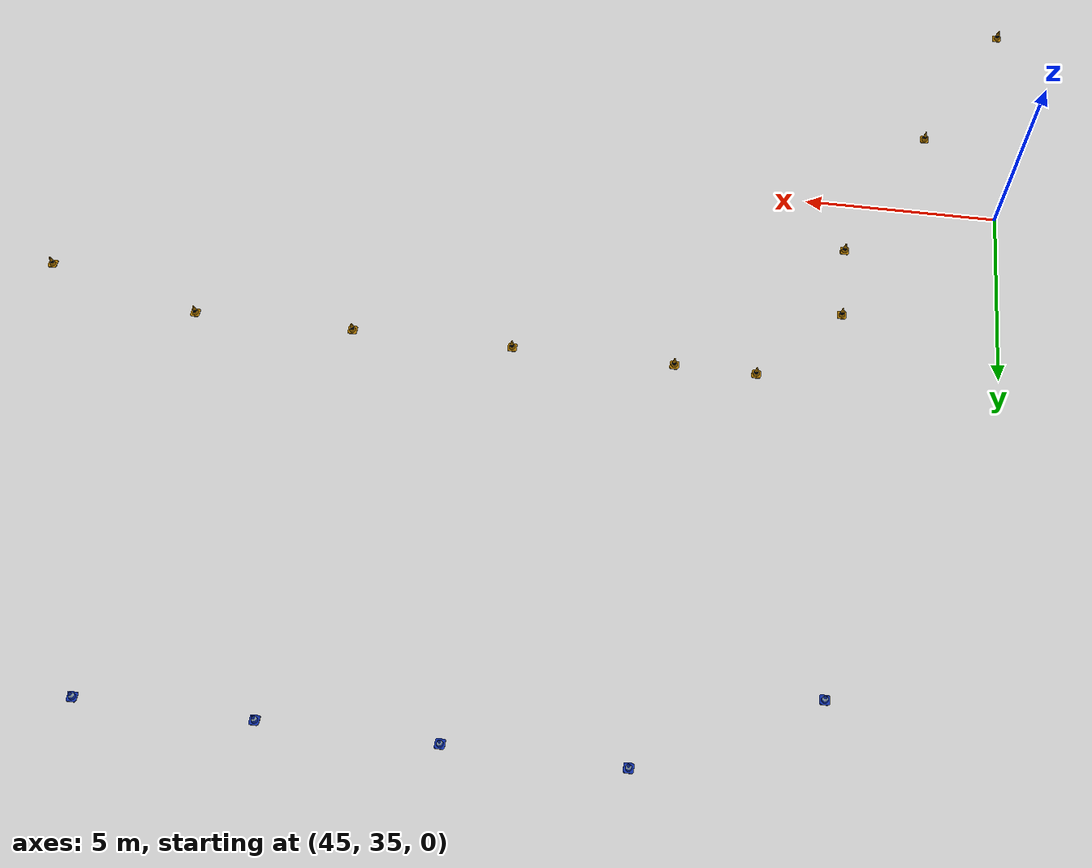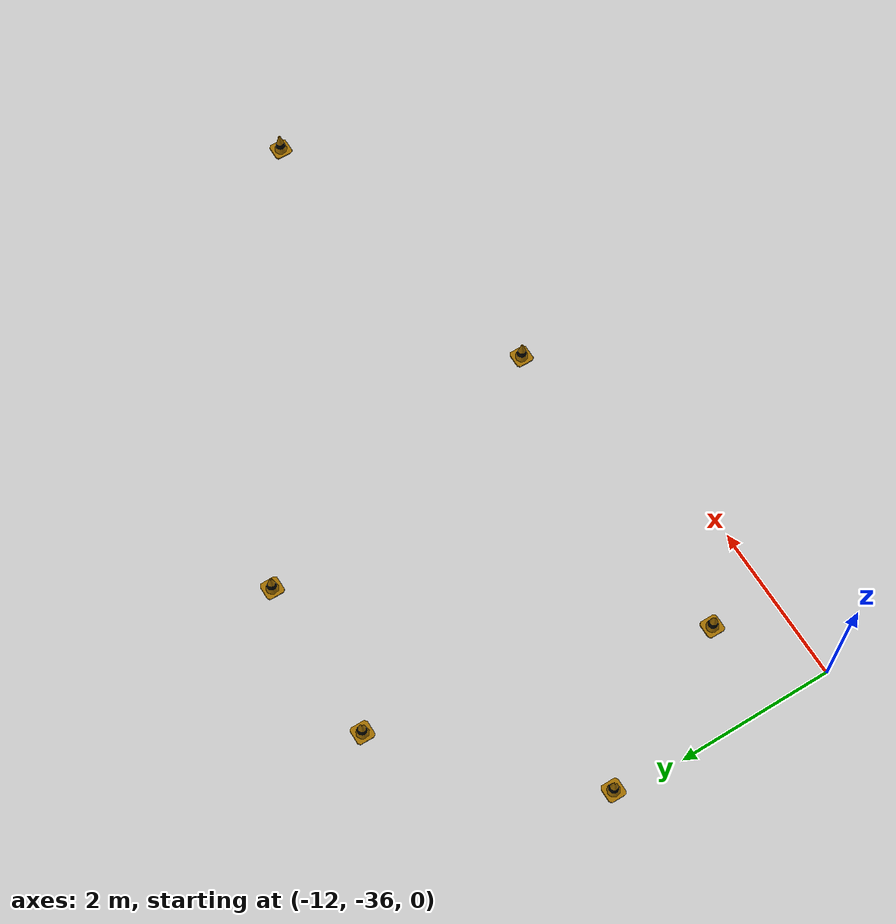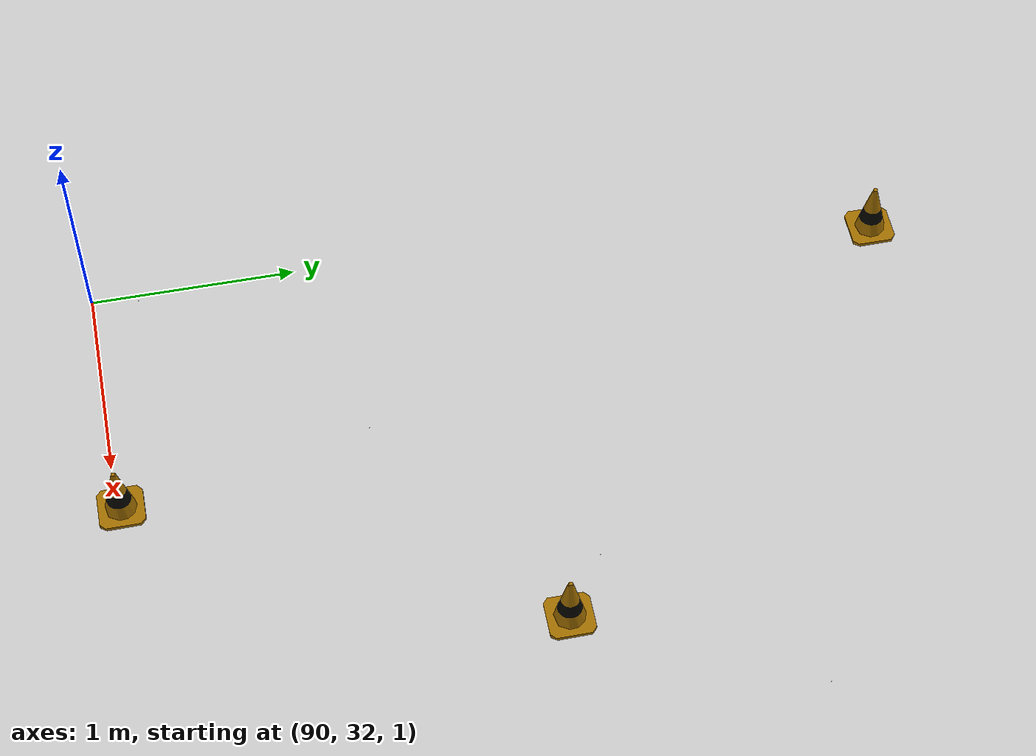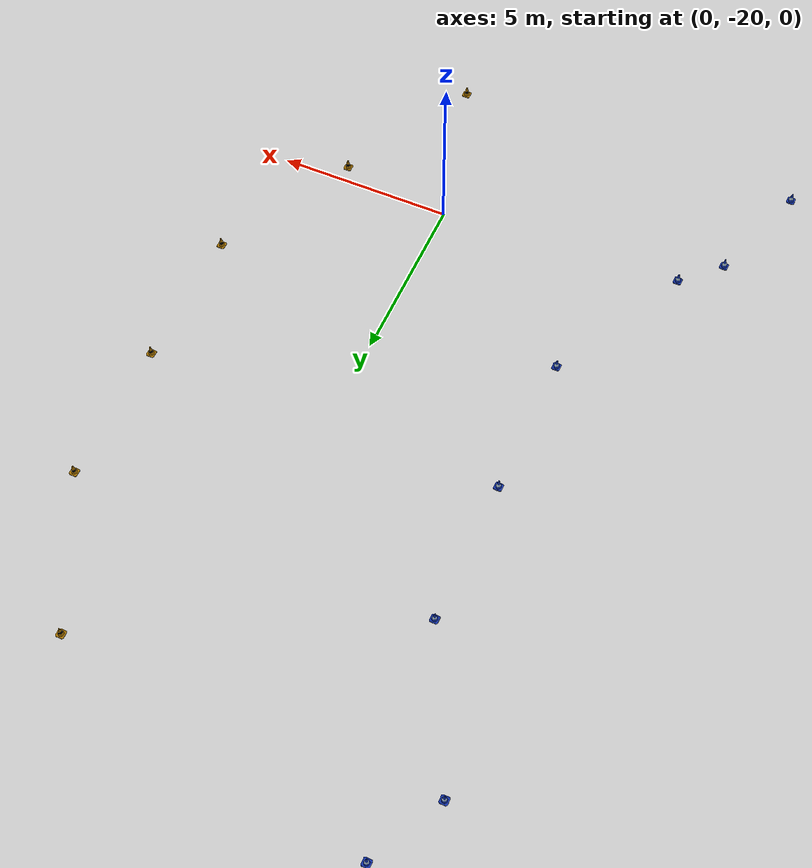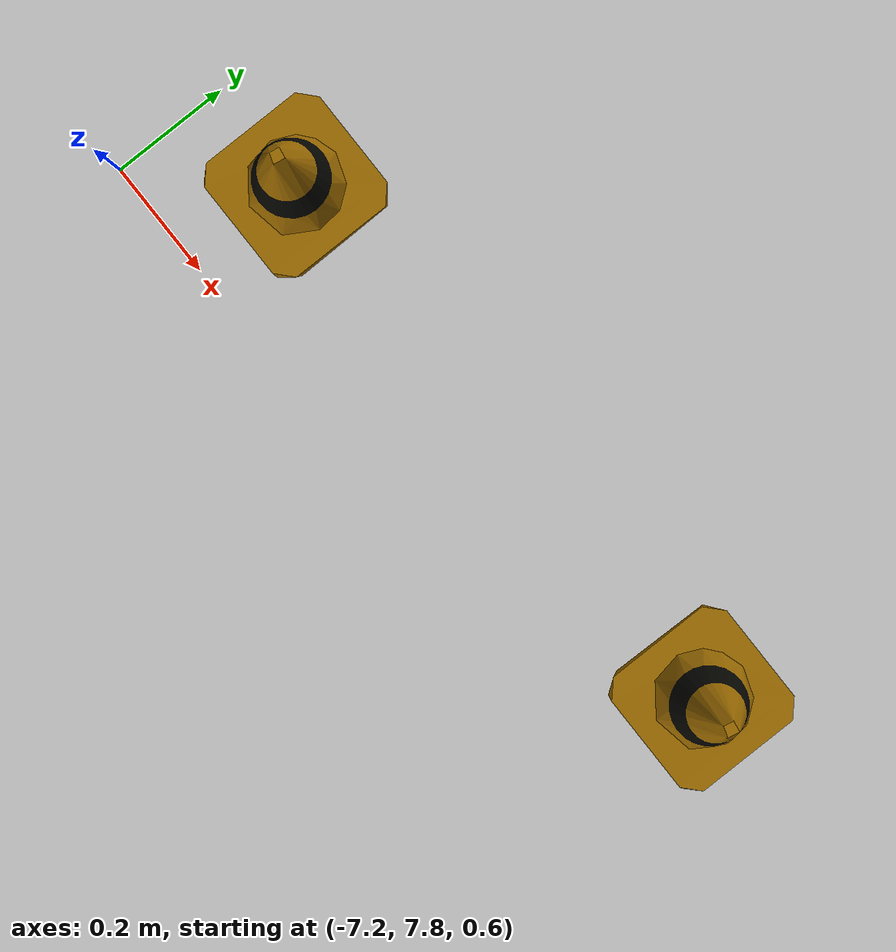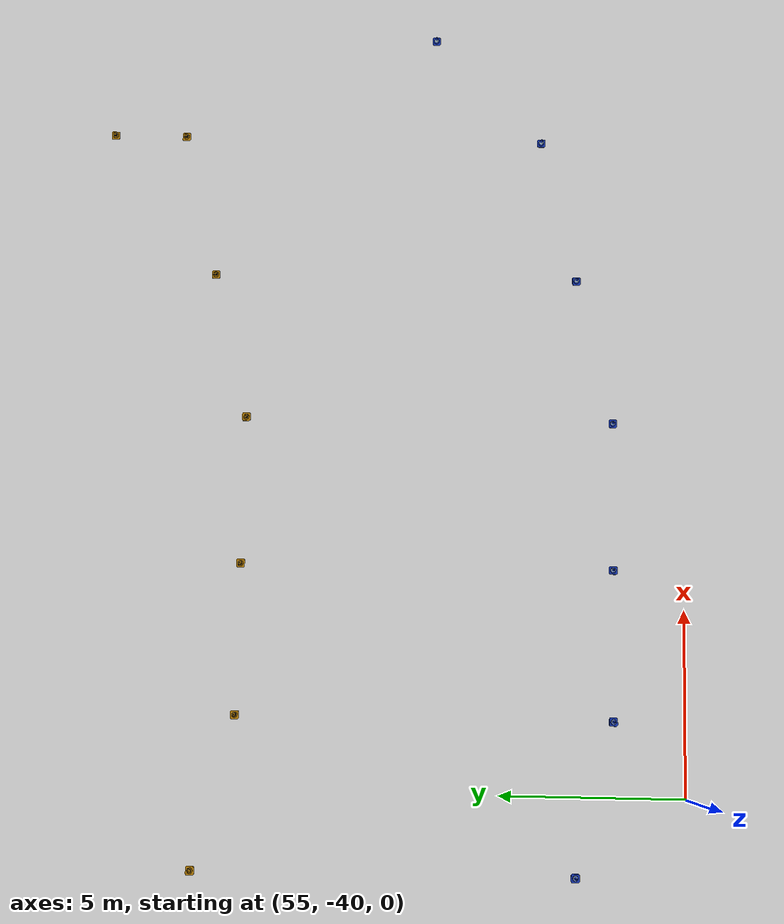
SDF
<sdf version='1.6'>
  <world name='rand_CT'>
    <gui fullscreen='0'>
      <camera name='user_camera'>
        <pose frame=''>-40 40 20 0 0.667643 -1</pose>
        <view_controller>orbit</view_controller>
        <projection_type>perspective</projection_type>
      </camera>
    </gui>

    <!-- WORLD SETTINGS -->
    <scene>
      <sky>
        <clouds>
          <speed>3</speed>
        </clouds>
      </sky>
      <ambient>1.0 1.0 1.0 1.0</ambient>
      <shadows>false</shadows>
    </scene>

    <light name='sun' type='directional'>
      <cast_shadows>1</cast_shadows>
      <pose frame=''>0 0 10 0 -0 0</pose>
      <diffuse>0.8 0.8 0.8 1</diffuse>
      <specular>0.1 0.1 0.1 1</specular>
      <attenuation>
        <range>1000</range>
        <constant>0.9</constant>
        <linear>0.01</linear>
        <quadratic>0.001</quadratic>
      </attenuation>
      <direction>-0.5 0.5 -1</direction>
    </light>

    <!-- MODELS -->
    <include>
      <uri>model://models/ground_plane</uri>
      <pose>0.0 0.0 0.0 0 0 0</pose>
    </include>

    <include>
      <uri>model://models/rand_CT</uri>
      <pose>0 0 0.5 0 0 0</pose>
    </include>

  </world>
</sdf>

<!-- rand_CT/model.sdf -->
<sdf version='1.6'>
  <model name='rand_CT'>

    <link name='link_0_clone_0'>
      <pose frame=''>-45 30 0.15 0 -0 0</pose>

      <collision name="collision">
        <geometry>
          <mesh>
            <uri>model://eufs_description/meshes/cone_blue.dae</uri>
          </mesh>
        </geometry>
      </collision>

      <visual name="visual">
        <geometry>
          <mesh>
            <uri>model://eufs_description/meshes/cone_blue.dae</uri>
          </mesh>
        </geometry>
      </visual>
    </link>

    <link name='link_0_clone_1'>
      <pose frame=''>-45 34 0.15 0 -0 0</pose>

      <collision name="collision">
        <geometry>
          <mesh>
            <uri>model://eufs_description/meshes/cone_blue.dae</uri>
          </mesh>
        </geometry>
      </collision>

      <visual name="visual">
        <geometry>
          <mesh>
            <uri>model://eufs_description/meshes/cone_blue.dae</uri>
          </mesh>
        </geometry>
      </visual>
    </link>

    <link name='link_0_clone_2'>
      <pose frame=''>-45 38 0.15 0 -0 0</pose>

      <collision name="collision">
        <geometry>
          <mesh>
            <uri>model://eufs_description/meshes/cone_blue.dae</uri>
          </mesh>
        </geometry>
      </collision>

      <visual name="visual">
        <geometry>
          <mesh>
            <uri>model://eufs_description/meshes/cone_blue.dae</uri>
          </mesh>
        </geometry>
      </visual>
    </link>

    <link name='link_0_clone_3'>
      <pose frame=''>-44 26 0.15 0 -0 0</pose>

      <collision name="collision">
        <geometry>
          <mesh>
            <uri>model://eufs_description/meshes/cone_blue.dae</uri>
          </mesh>
        </geometry>
      </collision>

      <visual name="visual">
        <geometry>
          <mesh>
            <uri>model://eufs_description/meshes/cone_blue.dae</uri>
          </mesh>
        </geometry>
      </visual>
    </link>

    <link name='link_0_clone_4'>
      <pose frame=''>-44 42 0.15 0 -0 0</pose>

      <collision name="collision">
        <geometry>
          <mesh>
            <uri>model://eufs_description/meshes/cone_blue.dae</uri>
          </mesh>
        </geometry>
      </collision>

      <visual name="visual">
        <geometry>
          <mesh>
            <uri>model://eufs_description/meshes/cone_blue.dae</uri>
          </mesh>
        </geometry>
      </visual>
    </link>

    <link name='link_0_clone_5'>
      <pose frame=''>-42 46 0.15 0 -0 0</pose>

      <collision name="collision">
        <geometry>
          <mesh>
            <uri>model://eufs_description/meshes/cone_blue.dae</uri>
          </mesh>
        </geometry>
      </collision>

      <visual name="visual">
        <geometry>
          <mesh>
            <uri>model://eufs_description/meshes/cone_blue.dae</uri>
          </mesh>
        </geometry>
      </visual>
    </link>

    <link name='link_0_clone_6'>
      <pose frame=''>-39 49 0.15 0 -0 0</pose>

      <collision name="collision">
        <geometry>
          <mesh>
            <uri>model://eufs_description/meshes/cone_blue.dae</uri>
          </mesh>
        </geometry>
      </collision>

      <visual name="visual">
        <geometry>
          <mesh>
            <uri>model://eufs_description/meshes/cone_blue.dae</uri>
          </mesh>
        </geometry>
      </visual>
    </link>

    <link name='link_0_clone_7'>
      <pose frame=''>-36 18 0.15 0 -0 0</pose>

      <collision name="collision">
        <geometry>
          <mesh>
            <uri>model://eufs_description/meshes/cone_blue.dae</uri>
          </mesh>
        </geometry>
      </collision>

      <visual name="visual">
        <geometry>
          <mesh>
            <uri>model://eufs_description/meshes/cone_blue.dae</uri>
          </mesh>
        </geometry>
      </visual>
    </link>

    <link name='link_0_clone_8'>
      <pose frame=''>-36 28 0.15 0 -0 0</pose>

      <collision name="collision">
        <geometry>
          <mesh>
            <uri>model://eufs_description/meshes/cone_yellow.dae</uri>
          </mesh>
        </geometry>
      </collision>

      <visual name="visual">
        <geometry>
          <mesh>
            <uri>model://eufs_description/meshes/cone_yellow.dae</uri>
          </mesh>
        </geometry>
      </visual>
    </link>

    <link name='link_0_clone_9'>
      <pose frame=''>-35 30 0.15 0 -0 0</pose>

      <collision name="collision">
        <geometry>
          <mesh>
            <uri>model://eufs_description/meshes/cone_yellow.dae</uri>
          </mesh>
        </geometry>
      </collision>

      <visual name="visual">
        <geometry>
          <mesh>
            <uri>model://eufs_description/meshes/cone_yellow.dae</uri>
          </mesh>
        </geometry>
      </visual>
    </link>

    <link name='link_0_clone_10'>
      <pose frame=''>-35 34 0.15 0 -0 0</pose>

      <collision name="collision">
        <geometry>
          <mesh>
            <uri>model://eufs_description/meshes/cone_yellow.dae</uri>
          </mesh>
        </geometry>
      </collision>

      <visual name="visual">
        <geometry>
          <mesh>
            <uri>model://eufs_description/meshes/cone_yellow.dae</uri>
          </mesh>
        </geometry>
      </visual>
    </link>

    <link name='link_0_clone_11'>
      <pose frame=''>-35 38 0.15 0 -0 0</pose>

      <collision name="collision">
        <geometry>
          <mesh>
            <uri>model://eufs_description/meshes/cone_yellow.dae</uri>
          </mesh>
        </geometry>
      </collision>

      <visual name="visual">
        <geometry>
          <mesh>
            <uri>model://eufs_description/meshes/cone_yellow.dae</uri>
          </mesh>
        </geometry>
      </visual>
    </link>

    <link name='link_0_clone_12'>
      <pose frame=''>-34 13 0.15 0 -0 0</pose>

      <collision name="collision">
        <geometry>
          <mesh>
            <uri>model://eufs_description/meshes/cone_blue.dae</uri>
          </mesh>
        </geometry>
      </collision>

      <visual name="visual">
        <geometry>
          <mesh>
            <uri>model://eufs_description/meshes/cone_blue.dae</uri>
          </mesh>
        </geometry>
      </visual>
    </link>

    <link name='link_0_clone_13'>
      <pose frame=''>-34 26 0.15 0 -0 0</pose>

      <collision name="collision">
        <geometry>
          <mesh>
            <uri>model://eufs_description/meshes/cone_yellow.dae</uri>
          </mesh>
        </geometry>
      </collision>

      <visual name="visual">
        <geometry>
          <mesh>
            <uri>model://eufs_description/meshes/cone_yellow.dae</uri>
          </mesh>
        </geometry>
      </visual>
    </link>

    <link name='link_0_clone_14'>
      <pose frame=''>-34 42 0.15 0 -0 0</pose>

      <collision name="collision">
        <geometry>
          <mesh>
            <uri>model://eufs_description/meshes/cone_yellow.dae</uri>
          </mesh>
        </geometry>
      </collision>

      <visual name="visual">
        <geometry>
          <mesh>
            <uri>model://eufs_description/meshes/cone_yellow.dae</uri>
          </mesh>
        </geometry>
      </visual>
    </link>

    <link name='link_0_clone_15'>
      <pose frame=''>-33 15 0.15 0 -0 0</pose>

      <collision name="collision">
        <geometry>
          <mesh>
            <uri>model://eufs_description/meshes/cone_blue.dae</uri>
          </mesh>
        </geometry>
      </collision>

      <visual name="visual">
        <geometry>
          <mesh>
            <uri>model://eufs_description/meshes/cone_blue.dae</uri>
          </mesh>
        </geometry>
      </visual>
    </link>

    <link name='link_0_clone_16'>
      <pose frame=''>-33 25 0.15 0 -0 0</pose>

      <collision name="collision">
        <geometry>
          <mesh>
            <uri>model://eufs_description/meshes/cone_yellow.dae</uri>
          </mesh>
        </geometry>
      </collision>

      <visual name="visual">
        <geometry>
          <mesh>
            <uri>model://eufs_description/meshes/cone_yellow.dae</uri>
          </mesh>
        </geometry>
      </visual>
    </link>

    <link name='link_0_clone_17'>
      <pose frame=''>-32 46 0.15 0 -0 0</pose>

      <collision name="collision">
        <geometry>
          <mesh>
            <uri>model://eufs_description/meshes/cone_yellow.dae</uri>
          </mesh>
        </geometry>
      </collision>

      <visual name="visual">
        <geometry>
          <mesh>
            <uri>model://eufs_description/meshes/cone_yellow.dae</uri>
          </mesh>
        </geometry>
      </visual>
    </link>

    <link name='link_0_clone_18'>
      <pose frame=''>-31 47 0.15 0 -0 0</pose>

      <collision name="collision">
        <geometry>
          <mesh>
            <uri>model://eufs_description/meshes/cone_yellow.dae</uri>
          </mesh>
        </geometry>
      </collision>

      <visual name="visual">
        <geometry>
          <mesh>
            <uri>model://eufs_description/meshes/cone_yellow.dae</uri>
          </mesh>
        </geometry>
      </visual>
    </link>

    <link name='link_0_clone_19'>
      <pose frame=''>-31 57 0.15 0 -0 0</pose>

      <collision name="collision">
        <geometry>
          <mesh>
            <uri>model://eufs_description/meshes/cone_blue.dae</uri>
          </mesh>
        </geometry>
      </collision>

      <visual name="visual">
        <geometry>
          <mesh>
            <uri>model://eufs_description/meshes/cone_blue.dae</uri>
          </mesh>
        </geometry>
      </visual>
    </link>

    <link name='link_0_clone_20'>
      <pose frame=''>-30 11 0.15 0 -0 0</pose>

      <collision name="collision">
        <geometry>
          <mesh>
            <uri>model://eufs_description/meshes/cone_blue.dae</uri>
          </mesh>
        </geometry>
      </collision>

      <visual name="visual">
        <geometry>
          <mesh>
            <uri>model://eufs_description/meshes/cone_blue.dae</uri>
          </mesh>
        </geometry>
      </visual>
    </link>

    <link name='link_0_clone_21'>
      <pose frame=''>-29 49 0.15 0 -0 0</pose>

      <collision name="collision">
        <geometry>
          <mesh>
            <uri>model://eufs_description/meshes/cone_yellow.dae</uri>
          </mesh>
        </geometry>
      </collision>

      <visual name="visual">
        <geometry>
          <mesh>
            <uri>model://eufs_description/meshes/cone_yellow.dae</uri>
          </mesh>
        </geometry>
      </visual>
    </link>

    <link name='link_0_clone_22'>
      <pose frame=''>-27 20 0.15 0 -0 0</pose>

      <collision name="collision">
        <geometry>
          <mesh>
            <uri>model://eufs_description/meshes/cone_yellow.dae</uri>
          </mesh>
        </geometry>
      </collision>

      <visual name="visual">
        <geometry>
          <mesh>
            <uri>model://eufs_description/meshes/cone_yellow.dae</uri>
          </mesh>
        </geometry>
      </visual>
    </link>

    <link name='link_0_clone_23'>
      <pose frame=''>-27 48 0.15 0 -0 0</pose>

      <collision name="collision">
        <geometry>
          <mesh>
            <uri>model://eufs_description/meshes/cone_yellow.dae</uri>
          </mesh>
        </geometry>
      </collision>

      <visual name="visual">
        <geometry>
          <mesh>
            <uri>model://eufs_description/meshes/cone_yellow.dae</uri>
          </mesh>
        </geometry>
      </visual>
    </link>

    <link name='link_0_clone_24'>
      <pose frame=''>-27 58 0.15 0 -0 0</pose>

      <collision name="collision">
        <geometry>
          <mesh>
            <uri>model://eufs_description/meshes/cone_blue.dae</uri>
          </mesh>
        </geometry>
      </collision>

      <visual name="visual">
        <geometry>
          <mesh>
            <uri>model://eufs_description/meshes/cone_blue.dae</uri>
          </mesh>
        </geometry>
      </visual>
    </link>

    <link name='link_0_clone_25'>
      <pose frame=''>-23 18 0.15 0 -0 0</pose>

      <collision name="collision">
        <geometry>
          <mesh>
            <uri>model://eufs_description/meshes/cone_yellow.dae</uri>
          </mesh>
        </geometry>
      </collision>

      <visual name="visual">
        <geometry>
          <mesh>
            <uri>model://eufs_description/meshes/cone_yellow.dae</uri>
          </mesh>
        </geometry>
      </visual>
    </link>

    <link name='link_0_clone_26'>
      <pose frame=''>-23 49 0.15 0 -0 0</pose>

      <collision name="collision">
        <geometry>
          <mesh>
            <uri>model://eufs_description/meshes/cone_yellow.dae</uri>
          </mesh>
        </geometry>
      </collision>

      <visual name="visual">
        <geometry>
          <mesh>
            <uri>model://eufs_description/meshes/cone_yellow.dae</uri>
          </mesh>
        </geometry>
      </visual>
    </link>

    <link name='link_0_clone_27'>
      <pose frame=''>-23 59 0.15 0 -0 0</pose>

      <collision name="collision">
        <geometry>
          <mesh>
            <uri>model://eufs_description/meshes/cone_blue.dae</uri>
          </mesh>
        </geometry>
      </collision>

      <visual name="visual">
        <geometry>
          <mesh>
            <uri>model://eufs_description/meshes/cone_blue.dae</uri>
          </mesh>
        </geometry>
      </visual>
    </link>

    <link name='link_0_clone_28'>
      <pose frame=''>-22 6 0.15 0 -0 0</pose>

      <collision name="collision">
        <geometry>
          <mesh>
            <uri>model://eufs_description/meshes/cone_blue.dae</uri>
          </mesh>
        </geometry>
      </collision>

      <visual name="visual">
        <geometry>
          <mesh>
            <uri>model://eufs_description/meshes/cone_blue.dae</uri>
          </mesh>
        </geometry>
      </visual>
    </link>

    <link name='link_0_clone_29'>
      <pose frame=''>-22 8 0.15 0 -0 0</pose>

      <collision name="collision">
        <geometry>
          <mesh>
            <uri>model://eufs_description/meshes/cone_blue.dae</uri>
          </mesh>
        </geometry>
      </collision>

      <visual name="visual">
        <geometry>
          <mesh>
            <uri>model://eufs_description/meshes/cone_blue.dae</uri>
          </mesh>
        </geometry>
      </visual>
    </link>

    <link name='link_0_clone_30'>
      <pose frame=''>-22 18 0.15 0 -0 0</pose>

      <collision name="collision">
        <geometry>
          <mesh>
            <uri>model://eufs_description/meshes/cone_yellow.dae</uri>
          </mesh>
        </geometry>
      </collision>

      <visual name="visual">
        <geometry>
          <mesh>
            <uri>model://eufs_description/meshes/cone_yellow.dae</uri>
          </mesh>
        </geometry>
      </visual>
    </link>

    <link name='link_0_clone_31'>
      <pose frame=''>-21 -35 0.15 0 -0 0</pose>

      <collision name="collision">
        <geometry>
          <mesh>
            <uri>model://eufs_description/meshes/cone_blue.dae</uri>
          </mesh>
        </geometry>
      </collision>

      <visual name="visual">
        <geometry>
          <mesh>
            <uri>model://eufs_description/meshes/cone_blue.dae</uri>
          </mesh>
        </geometry>
      </visual>
    </link>

    <link name='link_0_clone_32'>
      <pose frame=''>-20 -39 0.15 0 -0 0</pose>

      <collision name="collision">
        <geometry>
          <mesh>
            <uri>model://eufs_description/meshes/cone_blue.dae</uri>
          </mesh>
        </geometry>
      </collision>

      <visual name="visual">
        <geometry>
          <mesh>
            <uri>model://eufs_description/meshes/cone_blue.dae</uri>
          </mesh>
        </geometry>
      </visual>
    </link>

    <link name='link_0_clone_33'>
      <pose frame=''>-20 -31 0.15 0 -0 0</pose>

      <collision name="collision">
        <geometry>
          <mesh>
            <uri>model://eufs_description/meshes/cone_blue.dae</uri>
          </mesh>
        </geometry>
      </collision>

      <visual name="visual">
        <geometry>
          <mesh>
            <uri>model://eufs_description/meshes/cone_blue.dae</uri>
          </mesh>
        </geometry>
      </visual>
    </link>

    <link name='link_0_clone_34'>
      <pose frame=''>-19 49 0.15 0 -0 0</pose>

      <collision name="collision">
        <geometry>
          <mesh>
            <uri>model://eufs_description/meshes/cone_yellow.dae</uri>
          </mesh>
        </geometry>
      </collision>

      <visual name="visual">
        <geometry>
          <mesh>
            <uri>model://eufs_description/meshes/cone_yellow.dae</uri>
          </mesh>
        </geometry>
      </visual>
    </link>

    <link name='link_0_clone_35'>
      <pose frame=''>-19 59 0.15 0 -0 0</pose>

      <collision name="collision">
        <geometry>
          <mesh>
            <uri>model://eufs_description/meshes/cone_blue.dae</uri>
          </mesh>
        </geometry>
      </collision>

      <visual name="visual">
        <geometry>
          <mesh>
            <uri>model://eufs_description/meshes/cone_blue.dae</uri>
          </mesh>
        </geometry>
      </visual>
    </link>

    <link name='link_0_clone_36'>
      <pose frame=''>-15 13 0.15 0 -0 0</pose>

      <collision name="collision">
        <geometry>
          <mesh>
            <uri>model://eufs_description/meshes/cone_yellow.dae</uri>
          </mesh>
        </geometry>
      </collision>

      <visual name="visual">
        <geometry>
          <mesh>
            <uri>model://eufs_description/meshes/cone_yellow.dae</uri>
          </mesh>
        </geometry>
      </visual>
    </link>

    <link name='link_0_clone_37'>
      <pose frame=''>-15 48 0.15 0 -0 0</pose>

      <collision name="collision">
        <geometry>
          <mesh>
            <uri>model://eufs_description/meshes/cone_yellow.dae</uri>
          </mesh>
        </geometry>
      </collision>

      <visual name="visual">
        <geometry>
          <mesh>
            <uri>model://eufs_description/meshes/cone_yellow.dae</uri>
          </mesh>
        </geometry>
      </visual>
    </link>

    <link name='link_0_clone_38'>
      <pose frame=''>-15 58 0.15 0 -0 0</pose>

      <collision name="collision">
        <geometry>
          <mesh>
            <uri>model://eufs_description/meshes/cone_blue.dae</uri>
          </mesh>
        </geometry>
      </collision>

      <visual name="visual">
        <geometry>
          <mesh>
            <uri>model://eufs_description/meshes/cone_blue.dae</uri>
          </mesh>
        </geometry>
      </visual>
    </link>

    <link name='link_0_clone_39'>
      <pose frame=''>-14 1 0.15 0 -0 0</pose>

      <collision name="collision">
        <geometry>
          <mesh>
            <uri>model://eufs_description/meshes/cone_blue.dae</uri>
          </mesh>
        </geometry>
      </collision>

      <visual name="visual">
        <geometry>
          <mesh>
            <uri>model://eufs_description/meshes/cone_blue.dae</uri>
          </mesh>
        </geometry>
      </visual>
    </link>

    <link name='link_0_clone_40'>
      <pose frame=''>-14 3 0.15 0 -0 0</pose>

      <collision name="collision">
        <geometry>
          <mesh>
            <uri>model://eufs_description/meshes/cone_blue.dae</uri>
          </mesh>
        </geometry>
      </collision>

      <visual name="visual">
        <geometry>
          <mesh>
            <uri>model://eufs_description/meshes/cone_blue.dae</uri>
          </mesh>
        </geometry>
      </visual>
    </link>

    <link name='link_0_clone_41'>
      <pose frame=''>-14 13 0.15 0 -0 0</pose>

      <collision name="collision">
        <geometry>
          <mesh>
            <uri>model://eufs_description/meshes/cone_yellow.dae</uri>
          </mesh>
        </geometry>
      </collision>

      <visual name="visual">
        <geometry>
          <mesh>
            <uri>model://eufs_description/meshes/cone_yellow.dae</uri>
          </mesh>
        </geometry>
      </visual>
    </link>

    <link name='link_0_clone_42'>
      <pose frame=''>-12 -33 0.15 0 -0 0</pose>

      <collision name="collision">
        <geometry>
          <mesh>
            <uri>model://eufs_description/meshes/cone_yellow.dae</uri>
          </mesh>
        </geometry>
      </collision>

      <visual name="visual">
        <geometry>
          <mesh>
            <uri>model://eufs_description/meshes/cone_yellow.dae</uri>
          </mesh>
        </geometry>
      </visual>
    </link>

    <link name='link_0_clone_43'>
      <pose frame=''>-12 -23 0.15 0 -0 0</pose>

      <collision name="collision">
        <geometry>
          <mesh>
            <uri>model://eufs_description/meshes/cone_blue.dae</uri>
          </mesh>
        </geometry>
      </collision>

      <visual name="visual">
        <geometry>
          <mesh>
            <uri>model://eufs_description/meshes/cone_blue.dae</uri>
          </mesh>
        </geometry>
      </visual>
    </link>

    <link name='link_0_clone_44'>
      <pose frame=''>-12 45 0.15 0 -0 0</pose>

      <collision name="collision">
        <geometry>
          <mesh>
            <uri>model://eufs_description/meshes/cone_yellow.dae</uri>
          </mesh>
        </geometry>
      </collision>

      <visual name="visual">
        <geometry>
          <mesh>
            <uri>model://eufs_description/meshes/cone_yellow.dae</uri>
          </mesh>
        </geometry>
      </visual>
    </link>

    <link name='link_0_clone_45'>
      <pose frame=''>-11 -45 0.15 0 -0 0</pose>

      <collision name="collision">
        <geometry>
          <mesh>
            <uri>model://eufs_description/meshes/cone_blue.dae</uri>
          </mesh>
        </geometry>
      </collision>

      <visual name="visual">
        <geometry>
          <mesh>
            <uri>model://eufs_description/meshes/cone_blue.dae</uri>
          </mesh>
        </geometry>
      </visual>
    </link>

    <link name='link_0_clone_46'>
      <pose frame=''>-11 -35 0.15 0 -0 0</pose>

      <collision name="collision">
        <geometry>
          <mesh>
            <uri>model://eufs_description/meshes/cone_yellow.dae</uri>
          </mesh>
        </geometry>
      </collision>

      <visual name="visual">
        <geometry>
          <mesh>
            <uri>model://eufs_description/meshes/cone_yellow.dae</uri>
          </mesh>
        </geometry>
      </visual>
    </link>

    <link name='link_0_clone_47'>
      <pose frame=''>-10 -31 0.15 0 -0 0</pose>

      <collision name="collision">
        <geometry>
          <mesh>
            <uri>model://eufs_description/meshes/cone_yellow.dae</uri>
          </mesh>
        </geometry>
      </collision>

      <visual name="visual">
        <geometry>
          <mesh>
            <uri>model://eufs_description/meshes/cone_yellow.dae</uri>
          </mesh>
        </geometry>
      </visual>
    </link>

    <link name='link_0_clone_48'>
      <pose frame=''>-9 -24 0.15 0 -0 0</pose>

      <collision name="collision">
        <geometry>
          <mesh>
            <uri>model://eufs_description/meshes/cone_blue.dae</uri>
          </mesh>
        </geometry>
      </collision>

      <visual name="visual">
        <geometry>
          <mesh>
            <uri>model://eufs_description/meshes/cone_blue.dae</uri>
          </mesh>
        </geometry>
      </visual>
    </link>

    <link name='link_0_clone_49'>
      <pose frame=''>-8 -31 0.15 0 -0 0</pose>

      <collision name="collision">
        <geometry>
          <mesh>
            <uri>model://eufs_description/meshes/cone_yellow.dae</uri>
          </mesh>
        </geometry>
      </collision>

      <visual name="visual">
        <geometry>
          <mesh>
            <uri>model://eufs_description/meshes/cone_yellow.dae</uri>
          </mesh>
        </geometry>
      </visual>
    </link>

    <link name='link_0_clone_50'>
      <pose frame=''>-8 -21 0.15 0 -0 0</pose>

      <collision name="collision">
        <geometry>
          <mesh>
            <uri>model://eufs_description/meshes/cone_blue.dae</uri>
          </mesh>
        </geometry>
      </collision>

      <visual name="visual">
        <geometry>
          <mesh>
            <uri>model://eufs_description/meshes/cone_blue.dae</uri>
          </mesh>
        </geometry>
      </visual>
    </link>

    <link name='link_0_clone_51'>
      <pose frame=''>-8 42 0.15 0 -0 0</pose>

      <collision name="collision">
        <geometry>
          <mesh>
            <uri>model://eufs_description/meshes/cone_yellow.dae</uri>
          </mesh>
        </geometry>
      </collision>

      <visual name="visual">
        <geometry>
          <mesh>
            <uri>model://eufs_description/meshes/cone_yellow.dae</uri>
          </mesh>
        </geometry>
      </visual>
    </link>

    <link name='link_0_clone_52'>
      <pose frame=''>-7 -45 0.15 0 -0 0</pose>

      <collision name="collision">
        <geometry>
          <mesh>
            <uri>model://eufs_description/meshes/cone_blue.dae</uri>
          </mesh>
        </geometry>
      </collision>

      <visual name="visual">
        <geometry>
          <mesh>
            <uri>model://eufs_description/meshes/cone_blue.dae</uri>
          </mesh>
        </geometry>
      </visual>
    </link>

    <link name='link_0_clone_53'>
      <pose frame=''>-7 -35 0.15 0 -0 0</pose>

      <collision name="collision">
        <geometry>
          <mesh>
            <uri>model://eufs_description/meshes/cone_yellow.dae</uri>
          </mesh>
        </geometry>
      </collision>

      <visual name="visual">
        <geometry>
          <mesh>
            <uri>model://eufs_description/meshes/cone_yellow.dae</uri>
          </mesh>
        </geometry>
      </visual>
    </link>

    <link name='link_0_clone_54'>
      <pose frame=''>-7 -20 0.15 0 -0 0</pose>

      <collision name="collision">
        <geometry>
          <mesh>
            <uri>model://eufs_description/meshes/cone_blue.dae</uri>
          </mesh>
        </geometry>
      </collision>

      <visual name="visual">
        <geometry>
          <mesh>
            <uri>model://eufs_description/meshes/cone_blue.dae</uri>
          </mesh>
        </geometry>
      </visual>
    </link>

    <link name='link_0_clone_55'>
      <pose frame=''>-7 -4 0.15 0 -0 0</pose>

      <collision name="collision">
        <geometry>
          <mesh>
            <uri>model://eufs_description/meshes/cone_blue.dae</uri>
          </mesh>
        </geometry>
      </collision>

      <visual name="visual">
        <geometry>
          <mesh>
            <uri>model://eufs_description/meshes/cone_blue.dae</uri>
          </mesh>
        </geometry>
      </visual>
    </link>

    <link name='link_0_clone_56'>
      <pose frame=''>-7 8 0.15 0 -0 0</pose>

      <collision name="collision">
        <geometry>
          <mesh>
            <uri>model://eufs_description/meshes/cone_yellow.dae</uri>
          </mesh>
        </geometry>
      </collision>

      <visual name="visual">
        <geometry>
          <mesh>
            <uri>model://eufs_description/meshes/cone_yellow.dae</uri>
          </mesh>
        </geometry>
      </visual>
    </link>

    <link name='link_0_clone_57'>
      <pose frame=''>-6 -2 0.15 0 -0 0</pose>

      <collision name="collision">
        <geometry>
          <mesh>
            <uri>model://eufs_description/meshes/cone_blue.dae</uri>
          </mesh>
        </geometry>
      </collision>

      <visual name="visual">
        <geometry>
          <mesh>
            <uri>model://eufs_description/meshes/cone_blue.dae</uri>
          </mesh>
        </geometry>
      </visual>
    </link>

    <link name='link_0_clone_58'>
      <pose frame=''>-6 8 0.15 0 -0 0</pose>

      <collision name="collision">
        <geometry>
          <mesh>
            <uri>model://eufs_description/meshes/cone_yellow.dae</uri>
          </mesh>
        </geometry>
      </collision>

      <visual name="visual">
        <geometry>
          <mesh>
            <uri>model://eufs_description/meshes/cone_yellow.dae</uri>
          </mesh>
        </geometry>
      </visual>
    </link>

    <link name='link_0_clone_59'>
      <pose frame=''>-6 52 0.15 0 -0 0</pose>

      <collision name="collision">
        <geometry>
          <mesh>
            <uri>model://eufs_description/meshes/cone_blue.dae</uri>
          </mesh>
        </geometry>
      </collision>

      <visual name="visual">
        <geometry>
          <mesh>
            <uri>model://eufs_description/meshes/cone_blue.dae</uri>
          </mesh>
        </geometry>
      </visual>
    </link>

    <link name='link_0_clone_60'>
      <pose frame=''>-5 -16 0.15 0 -0 0</pose>

      <collision name="collision">
        <geometry>
          <mesh>
            <uri>model://eufs_description/meshes/cone_blue.dae</uri>
          </mesh>
        </geometry>
      </collision>

      <visual name="visual">
        <geometry>
          <mesh>
            <uri>model://eufs_description/meshes/cone_blue.dae</uri>
          </mesh>
        </geometry>
      </visual>
    </link>

    <link name='link_0_clone_61'>
      <pose frame=''>-5 -12 0.15 0 -0 0</pose>

      <collision name="collision">
        <geometry>
          <mesh>
            <uri>model://eufs_description/meshes/cone_blue.dae</uri>
          </mesh>
        </geometry>
      </collision>

      <visual name="visual">
        <geometry>
          <mesh>
            <uri>model://eufs_description/meshes/cone_blue.dae</uri>
          </mesh>
        </geometry>
      </visual>
    </link>

    <link name='link_0_clone_62'>
      <pose frame=''>-5 -8 0.15 0 -0 0</pose>

      <collision name="collision">
        <geometry>
          <mesh>
            <uri>model://eufs_description/meshes/cone_blue.dae</uri>
          </mesh>
        </geometry>
      </collision>

      <visual name="visual">
        <geometry>
          <mesh>
            <uri>model://eufs_description/meshes/cone_blue.dae</uri>
          </mesh>
        </geometry>
      </visual>
    </link>

    <link name='link_0_clone_63'>
      <pose frame=''>-5 39 0.15 0 -0 0</pose>

      <collision name="collision">
        <geometry>
          <mesh>
            <uri>model://eufs_description/meshes/cone_yellow.dae</uri>
          </mesh>
        </geometry>
      </collision>

      <visual name="visual">
        <geometry>
          <mesh>
            <uri>model://eufs_description/meshes/cone_yellow.dae</uri>
          </mesh>
        </geometry>
      </visual>
    </link>

    <link name='link_0_clone_64'>
      <pose frame=''>-5 52 0.15 0 -0 0</pose>

      <collision name="collision">
        <geometry>
          <mesh>
            <uri>model://eufs_description/meshes/cone_blue.dae</uri>
          </mesh>
        </geometry>
      </collision>

      <visual name="visual">
        <geometry>
          <mesh>
            <uri>model://eufs_description/meshes/cone_blue.dae</uri>
          </mesh>
        </geometry>
      </visual>
    </link>

    <link name='link_0_clone_65'>
      <pose frame=''>-3 -44 0.15 0 -0 0</pose>

      <collision name="collision">
        <geometry>
          <mesh>
            <uri>model://eufs_description/meshes/cone_blue.dae</uri>
          </mesh>
        </geometry>
      </collision>

      <visual name="visual">
        <geometry>
          <mesh>
            <uri>model://eufs_description/meshes/cone_blue.dae</uri>
          </mesh>
        </geometry>
      </visual>
    </link>

    <link name='link_0_clone_66'>
      <pose frame=''>-3 -34 0.15 0 -0 0</pose>

      <collision name="collision">
        <geometry>
          <mesh>
            <uri>model://eufs_description/meshes/cone_yellow.dae</uri>
          </mesh>
        </geometry>
      </collision>

      <visual name="visual">
        <geometry>
          <mesh>
            <uri>model://eufs_description/meshes/cone_yellow.dae</uri>
          </mesh>
        </geometry>
      </visual>
    </link>

    <link name='link_0_clone_67'>
      <pose frame=''>-3 5 0.15 0 -0 0</pose>

      <collision name="collision">
        <geometry>
          <mesh>
            <uri>model://eufs_description/meshes/cone_yellow.dae</uri>
          </mesh>
        </geometry>
      </collision>

      <visual name="visual">
        <geometry>
          <mesh>
            <uri>model://eufs_description/meshes/cone_yellow.dae</uri>
          </mesh>
        </geometry>
      </visual>
    </link>

    <link name='link_0_clone_68'>
      <pose frame=''>-1 36 0.15 0 -0 0</pose>

      <collision name="collision">
        <geometry>
          <mesh>
            <uri>model://eufs_description/meshes/cone_yellow.dae</uri>
          </mesh>
        </geometry>
      </collision>

      <visual name="visual">
        <geometry>
          <mesh>
            <uri>model://eufs_description/meshes/cone_yellow.dae</uri>
          </mesh>
        </geometry>
      </visual>
    </link>

    <link name='link_0_clone_69'>
      <pose frame=''>-1 49 0.15 0 -0 0</pose>

      <collision name="collision">
        <geometry>
          <mesh>
            <uri>model://eufs_description/meshes/cone_blue.dae</uri>
          </mesh>
        </geometry>
      </collision>

      <visual name="visual">
        <geometry>
          <mesh>
            <uri>model://eufs_description/meshes/cone_blue.dae</uri>
          </mesh>
        </geometry>
      </visual>
    </link>

    <link name='link_0_clone_70'>
      <pose frame=''>1 -24 0.15 0 -0 0</pose>

      <collision name="collision">
        <geometry>
          <mesh>
            <uri>model://eufs_description/meshes/cone_yellow.dae</uri>
          </mesh>
        </geometry>
      </collision>

      <visual name="visual">
        <geometry>
          <mesh>
            <uri>model://eufs_description/meshes/cone_yellow.dae</uri>
          </mesh>
        </geometry>
      </visual>
    </link>

    <link name='link_0_clone_71'>
      <pose frame=''>2 46 0.15 0 -0 0</pose>

      <collision name="collision">
        <geometry>
          <mesh>
            <uri>model://eufs_description/meshes/cone_blue.dae</uri>
          </mesh>
        </geometry>
      </collision>

      <visual name="visual">
        <geometry>
          <mesh>
            <uri>model://eufs_description/meshes/cone_blue.dae</uri>
          </mesh>
        </geometry>
      </visual>
    </link>

    <link name='link_0_clone_72'>
      <pose frame=''>3 -20 0.15 0 -0 0</pose>

      <collision name="collision">
        <geometry>
          <mesh>
            <uri>model://eufs_description/meshes/cone_yellow.dae</uri>
          </mesh>
        </geometry>
      </collision>

      <visual name="visual">
        <geometry>
          <mesh>
            <uri>model://eufs_description/meshes/cone_yellow.dae</uri>
          </mesh>
        </geometry>
      </visual>
    </link>

    <link name='link_0_clone_73'>
      <pose frame=''>3 -4 0.15 0 -0 0</pose>

      <collision name="collision">
        <geometry>
          <mesh>
            <uri>model://eufs_description/meshes/cone_yellow.dae</uri>
          </mesh>
        </geometry>
      </collision>

      <visual name="visual">
        <geometry>
          <mesh>
            <uri>model://eufs_description/meshes/cone_yellow.dae</uri>
          </mesh>
        </geometry>
      </visual>
    </link>

    <link name='link_0_clone_74'>
      <pose frame=''>3 33 0.15 0 -0 0</pose>

      <collision name="collision">
        <geometry>
          <mesh>
            <uri>model://eufs_description/meshes/cone_yellow.dae</uri>
          </mesh>
        </geometry>
      </collision>

      <visual name="visual">
        <geometry>
          <mesh>
            <uri>model://eufs_description/meshes/cone_yellow.dae</uri>
          </mesh>
        </geometry>
      </visual>
    </link>

    <link name='link_0_clone_75'>
      <pose frame=''>4 -41 0.15 0 -0 0</pose>

      <collision name="collision">
        <geometry>
          <mesh>
            <uri>model://eufs_description/meshes/cone_blue.dae</uri>
          </mesh>
        </geometry>
      </collision>

      <visual name="visual">
        <geometry>
          <mesh>
            <uri>model://eufs_description/meshes/cone_blue.dae</uri>
          </mesh>
        </geometry>
      </visual>
    </link>

    <link name='link_0_clone_76'>
      <pose frame=''>5 -41 0.15 0 -0 0</pose>

      <collision name="collision">
        <geometry>
          <mesh>
            <uri>model://eufs_description/meshes/cone_blue.dae</uri>
          </mesh>
        </geometry>
      </collision>

      <visual name="visual">
        <geometry>
          <mesh>
            <uri>model://eufs_description/meshes/cone_blue.dae</uri>
          </mesh>
        </geometry>
      </visual>
    </link>

    <link name='link_0_clone_77'>
      <pose frame=''>5 -31 0.15 0 -0 0</pose>

      <collision name="collision">
        <geometry>
          <mesh>
            <uri>model://eufs_description/meshes/cone_yellow.dae</uri>
          </mesh>
        </geometry>
      </collision>

      <visual name="visual">
        <geometry>
          <mesh>
            <uri>model://eufs_description/meshes/cone_yellow.dae</uri>
          </mesh>
        </geometry>
      </visual>
    </link>

    <link name='link_0_clone_78'>
      <pose frame=''>5 -16 0.15 0 -0 0</pose>

      <collision name="collision">
        <geometry>
          <mesh>
            <uri>model://eufs_description/meshes/cone_yellow.dae</uri>
          </mesh>
        </geometry>
      </collision>

      <visual name="visual">
        <geometry>
          <mesh>
            <uri>model://eufs_description/meshes/cone_yellow.dae</uri>
          </mesh>
        </geometry>
      </visual>
    </link>

    <link name='link_0_clone_79'>
      <pose frame=''>5 -12 0.15 0 -0 0</pose>

      <collision name="collision">
        <geometry>
          <mesh>
            <uri>model://eufs_description/meshes/cone_yellow.dae</uri>
          </mesh>
        </geometry>
      </collision>

      <visual name="visual">
        <geometry>
          <mesh>
            <uri>model://eufs_description/meshes/cone_yellow.dae</uri>
          </mesh>
        </geometry>
      </visual>
    </link>

    <link name='link_0_clone_80'>
      <pose frame=''>5 -8 0.15 0 -0 0</pose>

      <collision name="collision">
        <geometry>
          <mesh>
            <uri>model://eufs_description/meshes/cone_yellow.dae</uri>
          </mesh>
        </geometry>
      </collision>

      <visual name="visual">
        <geometry>
          <mesh>
            <uri>model://eufs_description/meshes/cone_yellow.dae</uri>
          </mesh>
        </geometry>
      </visual>
    </link>

    <link name='link_0_clone_81'>
      <pose frame=''>6 30 0.15 0 -0 0</pose>

      <collision name="collision">
        <geometry>
          <mesh>
            <uri>model://eufs_description/meshes/cone_yellow.dae</uri>
          </mesh>
        </geometry>
      </collision>

      <visual name="visual">
        <geometry>
          <mesh>
            <uri>model://eufs_description/meshes/cone_yellow.dae</uri>
          </mesh>
        </geometry>
      </visual>
    </link>

    <link name='link_0_clone_82'>
      <pose frame=''>6 43 0.15 0 -0 0</pose>

      <collision name="collision">
        <geometry>
          <mesh>
            <uri>model://eufs_description/meshes/cone_blue.dae</uri>
          </mesh>
        </geometry>
      </collision>

      <visual name="visual">
        <geometry>
          <mesh>
            <uri>model://eufs_description/meshes/cone_blue.dae</uri>
          </mesh>
        </geometry>
      </visual>
    </link>

    <link name='link_0_clone_83'>
      <pose frame=''>9 -40 0.15 0 -0 0</pose>

      <collision name="collision">
        <geometry>
          <mesh>
            <uri>model://eufs_description/meshes/cone_blue.dae</uri>
          </mesh>
        </geometry>
      </collision>

      <visual name="visual">
        <geometry>
          <mesh>
            <uri>model://eufs_description/meshes/cone_blue.dae</uri>
          </mesh>
        </geometry>
      </visual>
    </link>

    <link name='link_0_clone_84'>
      <pose frame=''>9 -30 0.15 0 -0 0</pose>

      <collision name="collision">
        <geometry>
          <mesh>
            <uri>model://eufs_description/meshes/cone_yellow.dae</uri>
          </mesh>
        </geometry>
      </collision>

      <visual name="visual">
        <geometry>
          <mesh>
            <uri>model://eufs_description/meshes/cone_yellow.dae</uri>
          </mesh>
        </geometry>
      </visual>
    </link>

    <link name='link_0_clone_85'>
      <pose frame=''>10 27 0.15 0 -0 0</pose>

      <collision name="collision">
        <geometry>
          <mesh>
            <uri>model://eufs_description/meshes/cone_yellow.dae</uri>
          </mesh>
        </geometry>
      </collision>

      <visual name="visual">
        <geometry>
          <mesh>
            <uri>model://eufs_description/meshes/cone_yellow.dae</uri>
          </mesh>
        </geometry>
      </visual>
    </link>

    <link name='link_0_clone_86'>
      <pose frame=''>10 40 0.15 0 -0 0</pose>

      <collision name="collision">
        <geometry>
          <mesh>
            <uri>model://eufs_description/meshes/cone_blue.dae</uri>
          </mesh>
        </geometry>
      </collision>

      <visual name="visual">
        <geometry>
          <mesh>
            <uri>model://eufs_description/meshes/cone_blue.dae</uri>
          </mesh>
        </geometry>
      </visual>
    </link>

    <link name='link_0_clone_87'>
      <pose frame=''>13 -39 0.15 0 -0 0</pose>

      <collision name="collision">
        <geometry>
          <mesh>
            <uri>model://eufs_description/meshes/cone_blue.dae</uri>
          </mesh>
        </geometry>
      </collision>

      <visual name="visual">
        <geometry>
          <mesh>
            <uri>model://eufs_description/meshes/cone_blue.dae</uri>
          </mesh>
        </geometry>
      </visual>
    </link>

    <link name='link_0_clone_88'>
      <pose frame=''>13 -29 0.15 0 -0 0</pose>

      <collision name="collision">
        <geometry>
          <mesh>
            <uri>model://eufs_description/meshes/cone_yellow.dae</uri>
          </mesh>
        </geometry>
      </collision>

      <visual name="visual">
        <geometry>
          <mesh>
            <uri>model://eufs_description/meshes/cone_yellow.dae</uri>
          </mesh>
        </geometry>
      </visual>
    </link>

    <link name='link_0_clone_89'>
      <pose frame=''>13 24 0.15 0 -0 0</pose>

      <collision name="collision">
        <geometry>
          <mesh>
            <uri>model://eufs_description/meshes/cone_yellow.dae</uri>
          </mesh>
        </geometry>
      </collision>

      <visual name="visual">
        <geometry>
          <mesh>
            <uri>model://eufs_description/meshes/cone_yellow.dae</uri>
          </mesh>
        </geometry>
      </visual>
    </link>

    <link name='link_0_clone_90'>
      <pose frame=''>13 37 0.15 0 -0 0</pose>

      <collision name="collision">
        <geometry>
          <mesh>
            <uri>model://eufs_description/meshes/cone_blue.dae</uri>
          </mesh>
        </geometry>
      </collision>

      <visual name="visual">
        <geometry>
          <mesh>
            <uri>model://eufs_description/meshes/cone_blue.dae</uri>
          </mesh>
        </geometry>
      </visual>
    </link>

    <link name='link_0_clone_91'>
      <pose frame=''>16 -37 0.15 0 -0 0</pose>

      <collision name="collision">
        <geometry>
          <mesh>
            <uri>model://eufs_description/meshes/cone_blue.dae</uri>
          </mesh>
        </geometry>
      </collision>

      <visual name="visual">
        <geometry>
          <mesh>
            <uri>model://eufs_description/meshes/cone_blue.dae</uri>
          </mesh>
        </geometry>
      </visual>
    </link>

    <link name='link_0_clone_92'>
      <pose frame=''>17 -37 0.15 0 -0 0</pose>

      <collision name="collision">
        <geometry>
          <mesh>
            <uri>model://eufs_description/meshes/cone_blue.dae</uri>
          </mesh>
        </geometry>
      </collision>

      <visual name="visual">
        <geometry>
          <mesh>
            <uri>model://eufs_description/meshes/cone_blue.dae</uri>
          </mesh>
        </geometry>
      </visual>
    </link>

    <link name='link_0_clone_93'>
      <pose frame=''>17 -27 0.15 0 -0 0</pose>

      <collision name="collision">
        <geometry>
          <mesh>
            <uri>model://eufs_description/meshes/cone_yellow.dae</uri>
          </mesh>
        </geometry>
      </collision>

      <visual name="visual">
        <geometry>
          <mesh>
            <uri>model://eufs_description/meshes/cone_yellow.dae</uri>
          </mesh>
        </geometry>
      </visual>
    </link>

    <link name='link_0_clone_94'>
      <pose frame=''>17 22 0.15 0 -0 0</pose>

      <collision name="collision">
        <geometry>
          <mesh>
            <uri>model://eufs_description/meshes/cone_yellow.dae</uri>
          </mesh>
        </geometry>
      </collision>

      <visual name="visual">
        <geometry>
          <mesh>
            <uri>model://eufs_description/meshes/cone_yellow.dae</uri>
          </mesh>
        </geometry>
      </visual>
    </link>

    <link name='link_0_clone_95'>
      <pose frame=''>17 34 0.15 0 -0 0</pose>

      <collision name="collision">
        <geometry>
          <mesh>
            <uri>model://eufs_description/meshes/cone_blue.dae</uri>
          </mesh>
        </geometry>
      </collision>

      <visual name="visual">
        <geometry>
          <mesh>
            <uri>model://eufs_description/meshes/cone_blue.dae</uri>
          </mesh>
        </geometry>
      </visual>
    </link>

    <link name='link_0_clone_96'>
      <pose frame=''>20 31 0.15 0 -0 0</pose>

      <collision name="collision">
        <geometry>
          <mesh>
            <uri>model://eufs_description/meshes/cone_blue.dae</uri>
          </mesh>
        </geometry>
      </collision>

      <visual name="visual">
        <geometry>
          <mesh>
            <uri>model://eufs_description/meshes/cone_blue.dae</uri>
          </mesh>
        </geometry>
      </visual>
    </link>

    <link name='link_0_clone_97'>
      <pose frame=''>21 -36 0.15 0 -0 0</pose>

      <collision name="collision">
        <geometry>
          <mesh>
            <uri>model://eufs_description/meshes/cone_blue.dae</uri>
          </mesh>
        </geometry>
      </collision>

      <visual name="visual">
        <geometry>
          <mesh>
            <uri>model://eufs_description/meshes/cone_blue.dae</uri>
          </mesh>
        </geometry>
      </visual>
    </link>

    <link name='link_0_clone_98'>
      <pose frame=''>21 -26 0.15 0 -0 0</pose>

      <collision name="collision">
        <geometry>
          <mesh>
            <uri>model://eufs_description/meshes/cone_yellow.dae</uri>
          </mesh>
        </geometry>
      </collision>

      <visual name="visual">
        <geometry>
          <mesh>
            <uri>model://eufs_description/meshes/cone_yellow.dae</uri>
          </mesh>
        </geometry>
      </visual>
    </link>

    <link name='link_0_clone_99'>
      <pose frame=''>24 29 0.15 0 -0 0</pose>

      <collision name="collision">
        <geometry>
          <mesh>
            <uri>model://eufs_description/meshes/cone_blue.dae</uri>
          </mesh>
        </geometry>
      </collision>

      <visual name="visual">
        <geometry>
          <mesh>
            <uri>model://eufs_description/meshes/cone_blue.dae</uri>
          </mesh>
        </geometry>
      </visual>
    </link>

    <link name='link_0_clone_100'>
      <pose frame=''>25 -36 0.15 0 -0 0</pose>

      <collision name="collision">
        <geometry>
          <mesh>
            <uri>model://eufs_description/meshes/cone_blue.dae</uri>
          </mesh>
        </geometry>
      </collision>

      <visual name="visual">
        <geometry>
          <mesh>
            <uri>model://eufs_description/meshes/cone_blue.dae</uri>
          </mesh>
        </geometry>
      </visual>
    </link>

    <link name='link_0_clone_101'>
      <pose frame=''>25 -26 0.15 0 -0 0</pose>

      <collision name="collision">
        <geometry>
          <mesh>
            <uri>model://eufs_description/meshes/cone_yellow.dae</uri>
          </mesh>
        </geometry>
      </collision>

      <visual name="visual">
        <geometry>
          <mesh>
            <uri>model://eufs_description/meshes/cone_yellow.dae</uri>
          </mesh>
        </geometry>
      </visual>
    </link>

    <link name='link_0_clone_102'>
      <pose frame=''>25 19 0.15 0 -0 0</pose>

      <collision name="collision">
        <geometry>
          <mesh>
            <uri>model://eufs_description/meshes/cone_yellow.dae</uri>
          </mesh>
        </geometry>
      </collision>

      <visual name="visual">
        <geometry>
          <mesh>
            <uri>model://eufs_description/meshes/cone_yellow.dae</uri>
          </mesh>
        </geometry>
      </visual>
    </link>

    <link name='link_0_clone_103'>
      <pose frame=''>25 29 0.15 0 -0 0</pose>

      <collision name="collision">
        <geometry>
          <mesh>
            <uri>model://eufs_description/meshes/cone_blue.dae</uri>
          </mesh>
        </geometry>
      </collision>

      <visual name="visual">
        <geometry>
          <mesh>
            <uri>model://eufs_description/meshes/cone_blue.dae</uri>
          </mesh>
        </geometry>
      </visual>
    </link>

    <link name='link_0_clone_104'>
      <pose frame=''>29 -36 0.15 0 -0 0</pose>

      <collision name="collision">
        <geometry>
          <mesh>
            <uri>model://eufs_description/meshes/cone_blue.dae</uri>
          </mesh>
        </geometry>
      </collision>

      <visual name="visual">
        <geometry>
          <mesh>
            <uri>model://eufs_description/meshes/cone_blue.dae</uri>
          </mesh>
        </geometry>
      </visual>
    </link>

    <link name='link_0_clone_105'>
      <pose frame=''>29 -26 0.15 0 -0 0</pose>

      <collision name="collision">
        <geometry>
          <mesh>
            <uri>model://eufs_description/meshes/cone_yellow.dae</uri>
          </mesh>
        </geometry>
      </collision>

      <visual name="visual">
        <geometry>
          <mesh>
            <uri>model://eufs_description/meshes/cone_yellow.dae</uri>
          </mesh>
        </geometry>
      </visual>
    </link>

    <link name='link_0_clone_106'>
      <pose frame=''>29 19 0.15 0 -0 0</pose>

      <collision name="collision">
        <geometry>
          <mesh>
            <uri>model://eufs_description/meshes/cone_yellow.dae</uri>
          </mesh>
        </geometry>
      </collision>

      <visual name="visual">
        <geometry>
          <mesh>
            <uri>model://eufs_description/meshes/cone_yellow.dae</uri>
          </mesh>
        </geometry>
      </visual>
    </link>

    <link name='link_0_clone_107'>
      <pose frame=''>29 29 0.15 0 -0 0</pose>

      <collision name="collision">
        <geometry>
          <mesh>
            <uri>model://eufs_description/meshes/cone_blue.dae</uri>
          </mesh>
        </geometry>
      </collision>

      <visual name="visual">
        <geometry>
          <mesh>
            <uri>model://eufs_description/meshes/cone_blue.dae</uri>
          </mesh>
        </geometry>
      </visual>
    </link>

    <link name='link_0_clone_108'>
      <pose frame=''>33 20 0.15 0 -0 0</pose>

      <collision name="collision">
        <geometry>
          <mesh>
            <uri>model://eufs_description/meshes/cone_yellow.dae</uri>
          </mesh>
        </geometry>
      </collision>

      <visual name="visual">
        <geometry>
          <mesh>
            <uri>model://eufs_description/meshes/cone_yellow.dae</uri>
          </mesh>
        </geometry>
      </visual>
    </link>

    <link name='link_0_clone_109'>
      <pose frame=''>33 30 0.15 0 -0 0</pose>

      <collision name="collision">
        <geometry>
          <mesh>
            <uri>model://eufs_description/meshes/cone_blue.dae</uri>
          </mesh>
        </geometry>
      </collision>

      <visual name="visual">
        <geometry>
          <mesh>
            <uri>model://eufs_description/meshes/cone_blue.dae</uri>
          </mesh>
        </geometry>
      </visual>
    </link>

    <link name='link_0_clone_110'>
      <pose frame=''>35 29 0.15 0 -0 0</pose>

      <collision name="collision">
        <geometry>
          <mesh>
            <uri>model://eufs_description/meshes/cone_blue.dae</uri>
          </mesh>
        </geometry>
      </collision>

      <visual name="visual">
        <geometry>
          <mesh>
            <uri>model://eufs_description/meshes/cone_blue.dae</uri>
          </mesh>
        </geometry>
      </visual>
    </link>

    <link name='link_0_clone_111'>
      <pose frame=''>36 -29 0.15 0 -0 0</pose>

      <collision name="collision">
        <geometry>
          <mesh>
            <uri>model://eufs_description/meshes/cone_yellow.dae</uri>
          </mesh>
        </geometry>
      </collision>

      <visual name="visual">
        <geometry>
          <mesh>
            <uri>model://eufs_description/meshes/cone_yellow.dae</uri>
          </mesh>
        </geometry>
      </visual>
    </link>

    <link name='link_0_clone_112'>
      <pose frame=''>37 -37 0.15 0 -0 0</pose>

      <collision name="collision">
        <geometry>
          <mesh>
            <uri>model://eufs_description/meshes/cone_blue.dae</uri>
          </mesh>
        </geometry>
      </collision>

      <visual name="visual">
        <geometry>
          <mesh>
            <uri>model://eufs_description/meshes/cone_blue.dae</uri>
          </mesh>
        </geometry>
      </visual>
    </link>

    <link name='link_0_clone_113'>
      <pose frame=''>37 -27 0.15 0 -0 0</pose>

      <collision name="collision">
        <geometry>
          <mesh>
            <uri>model://eufs_description/meshes/cone_yellow.dae</uri>
          </mesh>
        </geometry>
      </collision>

      <visual name="visual">
        <geometry>
          <mesh>
            <uri>model://eufs_description/meshes/cone_yellow.dae</uri>
          </mesh>
        </geometry>
      </visual>
    </link>

    <link name='link_0_clone_114'>
      <pose frame=''>37 33 0.15 0 -0 0</pose>

      <collision name="collision">
        <geometry>
          <mesh>
            <uri>model://eufs_description/meshes/cone_blue.dae</uri>
          </mesh>
        </geometry>
      </collision>

      <visual name="visual">
        <geometry>
          <mesh>
            <uri>model://eufs_description/meshes/cone_blue.dae</uri>
          </mesh>
        </geometry>
      </visual>
    </link>

    <link name='link_0_clone_115'>
      <pose frame=''>39 37 0.15 0 -0 0</pose>

      <collision name="collision">
        <geometry>
          <mesh>
            <uri>model://eufs_description/meshes/cone_blue.dae</uri>
          </mesh>
        </geometry>
      </collision>

      <visual name="visual">
        <geometry>
          <mesh>
            <uri>model://eufs_description/meshes/cone_blue.dae</uri>
          </mesh>
        </geometry>
      </visual>
    </link>

    <link name='link_0_clone_116'>
      <pose frame=''>41 -37 0.15 0 -0 0</pose>

      <collision name="collision">
        <geometry>
          <mesh>
            <uri>model://eufs_description/meshes/cone_blue.dae</uri>
          </mesh>
        </geometry>
      </collision>

      <visual name="visual">
        <geometry>
          <mesh>
            <uri>model://eufs_description/meshes/cone_blue.dae</uri>
          </mesh>
        </geometry>
      </visual>
    </link>

    <link name='link_0_clone_117'>
      <pose frame=''>41 -27 0.15 0 -0 0</pose>

      <collision name="collision">
        <geometry>
          <mesh>
            <uri>model://eufs_description/meshes/cone_yellow.dae</uri>
          </mesh>
        </geometry>
      </collision>

      <visual name="visual">
        <geometry>
          <mesh>
            <uri>model://eufs_description/meshes/cone_yellow.dae</uri>
          </mesh>
        </geometry>
      </visual>
    </link>

    <link name='link_0_clone_118'>
      <pose frame=''>41 41 0.15 0 -0 0</pose>

      <collision name="collision">
        <geometry>
          <mesh>
            <uri>model://eufs_description/meshes/cone_blue.dae</uri>
          </mesh>
        </geometry>
      </collision>

      <visual name="visual">
        <geometry>
          <mesh>
            <uri>model://eufs_description/meshes/cone_blue.dae</uri>
          </mesh>
        </geometry>
      </visual>
    </link>

    <link name='link_0_clone_119'>
      <pose frame=''>42 26 0.15 0 -0 0</pose>

      <collision name="collision">
        <geometry>
          <mesh>
            <uri>model://eufs_description/meshes/cone_yellow.dae</uri>
          </mesh>
        </geometry>
      </collision>

      <visual name="visual">
        <geometry>
          <mesh>
            <uri>model://eufs_description/meshes/cone_yellow.dae</uri>
          </mesh>
        </geometry>
      </visual>
    </link>

    <link name='link_0_clone_120'>
      <pose frame=''>45 -37 0.15 0 -0 0</pose>

      <collision name="collision">
        <geometry>
          <mesh>
            <uri>model://eufs_description/meshes/cone_blue.dae</uri>
          </mesh>
        </geometry>
      </collision>

      <visual name="visual">
        <geometry>
          <mesh>
            <uri>model://eufs_description/meshes/cone_blue.dae</uri>
          </mesh>
        </geometry>
      </visual>
    </link>

    <link name='link_0_clone_121'>
      <pose frame=''>45 -27 0.15 0 -0 0</pose>

      <collision name="collision">
        <geometry>
          <mesh>
            <uri>model://eufs_description/meshes/cone_yellow.dae</uri>
          </mesh>
        </geometry>
      </collision>

      <visual name="visual">
        <geometry>
          <mesh>
            <uri>model://eufs_description/meshes/cone_yellow.dae</uri>
          </mesh>
        </geometry>
      </visual>
    </link>

    <link name='link_0_clone_122'>
      <pose frame=''>45 29 0.15 0 -0 0</pose>

      <collision name="collision">
        <geometry>
          <mesh>
            <uri>model://eufs_description/meshes/cone_yellow.dae</uri>
          </mesh>
        </geometry>
      </collision>

      <visual name="visual">
        <geometry>
          <mesh>
            <uri>model://eufs_description/meshes/cone_yellow.dae</uri>
          </mesh>
        </geometry>
      </visual>
    </link>

    <link name='link_0_clone_123'>
      <pose frame=''>47 33 0.15 0 -0 0</pose>

      <collision name="collision">
        <geometry>
          <mesh>
            <uri>model://eufs_description/meshes/cone_yellow.dae</uri>
          </mesh>
        </geometry>
      </collision>

      <visual name="visual">
        <geometry>
          <mesh>
            <uri>model://eufs_description/meshes/cone_yellow.dae</uri>
          </mesh>
        </geometry>
      </visual>
    </link>

    <link name='link_0_clone_124'>
      <pose frame=''>49 -37 0.15 0 -0 0</pose>

      <collision name="collision">
        <geometry>
          <mesh>
            <uri>model://eufs_description/meshes/cone_blue.dae</uri>
          </mesh>
        </geometry>
      </collision>

      <visual name="visual">
        <geometry>
          <mesh>
            <uri>model://eufs_description/meshes/cone_blue.dae</uri>
          </mesh>
        </geometry>
      </visual>
    </link>

    <link name='link_0_clone_125'>
      <pose frame=''>49 -27 0.15 0 -0 0</pose>

      <collision name="collision">
        <geometry>
          <mesh>
            <uri>model://eufs_description/meshes/cone_yellow.dae</uri>
          </mesh>
        </geometry>
      </collision>

      <visual name="visual">
        <geometry>
          <mesh>
            <uri>model://eufs_description/meshes/cone_yellow.dae</uri>
          </mesh>
        </geometry>
      </visual>
    </link>

    <link name='link_0_clone_126'>
      <pose frame=''>49 37 0.15 0 -0 0</pose>

      <collision name="collision">
        <geometry>
          <mesh>
            <uri>model://eufs_description/meshes/cone_yellow.dae</uri>
          </mesh>
        </geometry>
      </collision>

      <visual name="visual">
        <geometry>
          <mesh>
            <uri>model://eufs_description/meshes/cone_yellow.dae</uri>
          </mesh>
        </geometry>
      </visual>
    </link>

    <link name='link_0_clone_127'>
      <pose frame=''>49 39 0.15 0 -0 0</pose>

      <collision name="collision">
        <geometry>
          <mesh>
            <uri>model://eufs_description/meshes/cone_yellow.dae</uri>
          </mesh>
        </geometry>
      </collision>

      <visual name="visual">
        <geometry>
          <mesh>
            <uri>model://eufs_description/meshes/cone_yellow.dae</uri>
          </mesh>
        </geometry>
      </visual>
    </link>

    <link name='link_0_clone_128'>
      <pose frame=''>49 49 0.15 0 -0 0</pose>

      <collision name="collision">
        <geometry>
          <mesh>
            <uri>model://eufs_description/meshes/cone_blue.dae</uri>
          </mesh>
        </geometry>
      </collision>

      <visual name="visual">
        <geometry>
          <mesh>
            <uri>model://eufs_description/meshes/cone_blue.dae</uri>
          </mesh>
        </geometry>
      </visual>
    </link>

    <link name='link_0_clone_129'>
      <pose frame=''>51 41 0.15 0 -0 0</pose>

      <collision name="collision">
        <geometry>
          <mesh>
            <uri>model://eufs_description/meshes/cone_yellow.dae</uri>
          </mesh>
        </geometry>
      </collision>

      <visual name="visual">
        <geometry>
          <mesh>
            <uri>model://eufs_description/meshes/cone_yellow.dae</uri>
          </mesh>
        </geometry>
      </visual>
    </link>

    <link name='link_0_clone_130'>
      <pose frame=''>53 -37 0.15 0 -0 0</pose>

      <collision name="collision">
        <geometry>
          <mesh>
            <uri>model://eufs_description/meshes/cone_blue.dae</uri>
          </mesh>
        </geometry>
      </collision>

      <visual name="visual">
        <geometry>
          <mesh>
            <uri>model://eufs_description/meshes/cone_blue.dae</uri>
          </mesh>
        </geometry>
      </visual>
    </link>

    <link name='link_0_clone_131'>
      <pose frame=''>53 -27 0.15 0 -0 0</pose>

      <collision name="collision">
        <geometry>
          <mesh>
            <uri>model://eufs_description/meshes/cone_yellow.dae</uri>
          </mesh>
        </geometry>
      </collision>

      <visual name="visual">
        <geometry>
          <mesh>
            <uri>model://eufs_description/meshes/cone_yellow.dae</uri>
          </mesh>
        </geometry>
      </visual>
    </link>

    <link name='link_0_clone_132'>
      <pose frame=''>53 41 0.15 0 -0 0</pose>

      <collision name="collision">
        <geometry>
          <mesh>
            <uri>model://eufs_description/meshes/cone_yellow.dae</uri>
          </mesh>
        </geometry>
      </collision>

      <visual name="visual">
        <geometry>
          <mesh>
            <uri>model://eufs_description/meshes/cone_yellow.dae</uri>
          </mesh>
        </geometry>
      </visual>
    </link>

    <link name='link_0_clone_133'>
      <pose frame=''>53 51 0.15 0 -0 0</pose>

      <collision name="collision">
        <geometry>
          <mesh>
            <uri>model://eufs_description/meshes/cone_blue.dae</uri>
          </mesh>
        </geometry>
      </collision>

      <visual name="visual">
        <geometry>
          <mesh>
            <uri>model://eufs_description/meshes/cone_blue.dae</uri>
          </mesh>
        </geometry>
      </visual>
    </link>

    <link name='link_0_clone_134'>
      <pose frame=''>57 -38 0.15 0 -0 0</pose>

      <collision name="collision">
        <geometry>
          <mesh>
            <uri>model://eufs_description/meshes/cone_blue.dae</uri>
          </mesh>
        </geometry>
      </collision>

      <visual name="visual">
        <geometry>
          <mesh>
            <uri>model://eufs_description/meshes/cone_blue.dae</uri>
          </mesh>
        </geometry>
      </visual>
    </link>

    <link name='link_0_clone_135'>
      <pose frame=''>57 -28 0.15 0 -0 0</pose>

      <collision name="collision">
        <geometry>
          <mesh>
            <uri>model://eufs_description/meshes/cone_yellow.dae</uri>
          </mesh>
        </geometry>
      </collision>

      <visual name="visual">
        <geometry>
          <mesh>
            <uri>model://eufs_description/meshes/cone_yellow.dae</uri>
          </mesh>
        </geometry>
      </visual>
    </link>

    <link name='link_0_clone_136'>
      <pose frame=''>57 41 0.15 0 -0 0</pose>

      <collision name="collision">
        <geometry>
          <mesh>
            <uri>model://eufs_description/meshes/cone_yellow.dae</uri>
          </mesh>
        </geometry>
      </collision>

      <visual name="visual">
        <geometry>
          <mesh>
            <uri>model://eufs_description/meshes/cone_yellow.dae</uri>
          </mesh>
        </geometry>
      </visual>
    </link>

    <link name='link_0_clone_137'>
      <pose frame=''>57 51 0.15 0 -0 0</pose>

      <collision name="collision">
        <geometry>
          <mesh>
            <uri>model://eufs_description/meshes/cone_blue.dae</uri>
          </mesh>
        </geometry>
      </collision>

      <visual name="visual">
        <geometry>
          <mesh>
            <uri>model://eufs_description/meshes/cone_blue.dae</uri>
          </mesh>
        </geometry>
      </visual>
    </link>

    <link name='link_0_clone_138'>
      <pose frame=''>61 -38 0.15 0 -0 0</pose>

      <collision name="collision">
        <geometry>
          <mesh>
            <uri>model://eufs_description/meshes/cone_blue.dae</uri>
          </mesh>
        </geometry>
      </collision>

      <visual name="visual">
        <geometry>
          <mesh>
            <uri>model://eufs_description/meshes/cone_blue.dae</uri>
          </mesh>
        </geometry>
      </visual>
    </link>

    <link name='link_0_clone_139'>
      <pose frame=''>61 -28 0.15 0 -0 0</pose>

      <collision name="collision">
        <geometry>
          <mesh>
            <uri>model://eufs_description/meshes/cone_yellow.dae</uri>
          </mesh>
        </geometry>
      </collision>

      <visual name="visual">
        <geometry>
          <mesh>
            <uri>model://eufs_description/meshes/cone_yellow.dae</uri>
          </mesh>
        </geometry>
      </visual>
    </link>

    <link name='link_0_clone_140'>
      <pose frame=''>61 41 0.15 0 -0 0</pose>

      <collision name="collision">
        <geometry>
          <mesh>
            <uri>model://eufs_description/meshes/cone_yellow.dae</uri>
          </mesh>
        </geometry>
      </collision>

      <visual name="visual">
        <geometry>
          <mesh>
            <uri>model://eufs_description/meshes/cone_yellow.dae</uri>
          </mesh>
        </geometry>
      </visual>
    </link>

    <link name='link_0_clone_141'>
      <pose frame=''>61 51 0.15 0 -0 0</pose>

      <collision name="collision">
        <geometry>
          <mesh>
            <uri>model://eufs_description/meshes/cone_blue.dae</uri>
          </mesh>
        </geometry>
      </collision>

      <visual name="visual">
        <geometry>
          <mesh>
            <uri>model://eufs_description/meshes/cone_blue.dae</uri>
          </mesh>
        </geometry>
      </visual>
    </link>

    <link name='link_0_clone_142'>
      <pose frame=''>65 -38 0.15 0 -0 0</pose>

      <collision name="collision">
        <geometry>
          <mesh>
            <uri>model://eufs_description/meshes/cone_blue.dae</uri>
          </mesh>
        </geometry>
      </collision>

      <visual name="visual">
        <geometry>
          <mesh>
            <uri>model://eufs_description/meshes/cone_blue.dae</uri>
          </mesh>
        </geometry>
      </visual>
    </link>

    <link name='link_0_clone_143'>
      <pose frame=''>65 -28 0.15 0 -0 0</pose>

      <collision name="collision">
        <geometry>
          <mesh>
            <uri>model://eufs_description/meshes/cone_yellow.dae</uri>
          </mesh>
        </geometry>
      </collision>

      <visual name="visual">
        <geometry>
          <mesh>
            <uri>model://eufs_description/meshes/cone_yellow.dae</uri>
          </mesh>
        </geometry>
      </visual>
    </link>

    <link name='link_0_clone_144'>
      <pose frame=''>65 41 0.15 0 -0 0</pose>

      <collision name="collision">
        <geometry>
          <mesh>
            <uri>model://eufs_description/meshes/cone_yellow.dae</uri>
          </mesh>
        </geometry>
      </collision>

      <visual name="visual">
        <geometry>
          <mesh>
            <uri>model://eufs_description/meshes/cone_yellow.dae</uri>
          </mesh>
        </geometry>
      </visual>
    </link>

    <link name='link_0_clone_145'>
      <pose frame=''>65 51 0.15 0 -0 0</pose>

      <collision name="collision">
        <geometry>
          <mesh>
            <uri>model://eufs_description/meshes/cone_blue.dae</uri>
          </mesh>
        </geometry>
      </collision>

      <visual name="visual">
        <geometry>
          <mesh>
            <uri>model://eufs_description/meshes/cone_blue.dae</uri>
          </mesh>
        </geometry>
      </visual>
    </link>

    <link name='link_0_clone_146'>
      <pose frame=''>69 -37 0.15 0 -0 0</pose>

      <collision name="collision">
        <geometry>
          <mesh>
            <uri>model://eufs_description/meshes/cone_blue.dae</uri>
          </mesh>
        </geometry>
      </collision>

      <visual name="visual">
        <geometry>
          <mesh>
            <uri>model://eufs_description/meshes/cone_blue.dae</uri>
          </mesh>
        </geometry>
      </visual>
    </link>

    <link name='link_0_clone_147'>
      <pose frame=''>69 -27 0.15 0 -0 0</pose>

      <collision name="collision">
        <geometry>
          <mesh>
            <uri>model://eufs_description/meshes/cone_yellow.dae</uri>
          </mesh>
        </geometry>
      </collision>

      <visual name="visual">
        <geometry>
          <mesh>
            <uri>model://eufs_description/meshes/cone_yellow.dae</uri>
          </mesh>
        </geometry>
      </visual>
    </link>

    <link name='link_0_clone_148'>
      <pose frame=''>69 40 0.15 0 -0 0</pose>

      <collision name="collision">
        <geometry>
          <mesh>
            <uri>model://eufs_description/meshes/cone_yellow.dae</uri>
          </mesh>
        </geometry>
      </collision>

      <visual name="visual">
        <geometry>
          <mesh>
            <uri>model://eufs_description/meshes/cone_yellow.dae</uri>
          </mesh>
        </geometry>
      </visual>
    </link>

    <link name='link_0_clone_149'>
      <pose frame=''>69 50 0.15 0 -0 0</pose>

      <collision name="collision">
        <geometry>
          <mesh>
            <uri>model://eufs_description/meshes/cone_blue.dae</uri>
          </mesh>
        </geometry>
      </collision>

      <visual name="visual">
        <geometry>
          <mesh>
            <uri>model://eufs_description/meshes/cone_blue.dae</uri>
          </mesh>
        </geometry>
      </visual>
    </link>

    <link name='link_0_clone_150'>
      <pose frame=''>73 -36 0.15 0 -0 0</pose>

      <collision name="collision">
        <geometry>
          <mesh>
            <uri>model://eufs_description/meshes/cone_blue.dae</uri>
          </mesh>
        </geometry>
      </collision>

      <visual name="visual">
        <geometry>
          <mesh>
            <uri>model://eufs_description/meshes/cone_blue.dae</uri>
          </mesh>
        </geometry>
      </visual>
    </link>

    <link name='link_0_clone_151'>
      <pose frame=''>73 -26 0.15 0 -0 0</pose>

      <collision name="collision">
        <geometry>
          <mesh>
            <uri>model://eufs_description/meshes/cone_yellow.dae</uri>
          </mesh>
        </geometry>
      </collision>

      <visual name="visual">
        <geometry>
          <mesh>
            <uri>model://eufs_description/meshes/cone_yellow.dae</uri>
          </mesh>
        </geometry>
      </visual>
    </link>

    <link name='link_0_clone_152'>
      <pose frame=''>73 -24 0.15 0 -0 0</pose>

      <collision name="collision">
        <geometry>
          <mesh>
            <uri>model://eufs_description/meshes/cone_yellow.dae</uri>
          </mesh>
        </geometry>
      </collision>

      <visual name="visual">
        <geometry>
          <mesh>
            <uri>model://eufs_description/meshes/cone_yellow.dae</uri>
          </mesh>
        </geometry>
      </visual>
    </link>

    <link name='link_0_clone_153'>
      <pose frame=''>73 40 0.15 0 -0 0</pose>

      <collision name="collision">
        <geometry>
          <mesh>
            <uri>model://eufs_description/meshes/cone_yellow.dae</uri>
          </mesh>
        </geometry>
      </collision>

      <visual name="visual">
        <geometry>
          <mesh>
            <uri>model://eufs_description/meshes/cone_yellow.dae</uri>
          </mesh>
        </geometry>
      </visual>
    </link>

    <link name='link_0_clone_154'>
      <pose frame=''>73 50 0.15 0 -0 0</pose>

      <collision name="collision">
        <geometry>
          <mesh>
            <uri>model://eufs_description/meshes/cone_blue.dae</uri>
          </mesh>
        </geometry>
      </collision>

      <visual name="visual">
        <geometry>
          <mesh>
            <uri>model://eufs_description/meshes/cone_blue.dae</uri>
          </mesh>
        </geometry>
      </visual>
    </link>

    <link name='link_0_clone_155'>
      <pose frame=''>76 -33 0.15 0 -0 0</pose>

      <collision name="collision">
        <geometry>
          <mesh>
            <uri>model://eufs_description/meshes/cone_blue.dae</uri>
          </mesh>
        </geometry>
      </collision>

      <visual name="visual">
        <geometry>
          <mesh>
            <uri>model://eufs_description/meshes/cone_blue.dae</uri>
          </mesh>
        </geometry>
      </visual>
    </link>

    <link name='link_0_clone_156'>
      <pose frame=''>76 -17 0.15 0 -0 0</pose>

      <collision name="collision">
        <geometry>
          <mesh>
            <uri>model://eufs_description/meshes/cone_yellow.dae</uri>
          </mesh>
        </geometry>
      </collision>

      <visual name="visual">
        <geometry>
          <mesh>
            <uri>model://eufs_description/meshes/cone_yellow.dae</uri>
          </mesh>
        </geometry>
      </visual>
    </link>

    <link name='link_0_clone_157'>
      <pose frame=''>77 40 0.15 0 -0 0</pose>

      <collision name="collision">
        <geometry>
          <mesh>
            <uri>model://eufs_description/meshes/cone_yellow.dae</uri>
          </mesh>
        </geometry>
      </collision>

      <visual name="visual">
        <geometry>
          <mesh>
            <uri>model://eufs_description/meshes/cone_yellow.dae</uri>
          </mesh>
        </geometry>
      </visual>
    </link>

    <link name='link_0_clone_158'>
      <pose frame=''>77 50 0.15 0 -0 0</pose>

      <collision name="collision">
        <geometry>
          <mesh>
            <uri>model://eufs_description/meshes/cone_blue.dae</uri>
          </mesh>
        </geometry>
      </collision>

      <visual name="visual">
        <geometry>
          <mesh>
            <uri>model://eufs_description/meshes/cone_blue.dae</uri>
          </mesh>
        </geometry>
      </visual>
    </link>

    <link name='link_0_clone_159'>
      <pose frame=''>78 -12 0.15 0 -0 0</pose>

      <collision name="collision">
        <geometry>
          <mesh>
            <uri>model://eufs_description/meshes/cone_yellow.dae</uri>
          </mesh>
        </geometry>
      </collision>

      <visual name="visual">
        <geometry>
          <mesh>
            <uri>model://eufs_description/meshes/cone_yellow.dae</uri>
          </mesh>
        </geometry>
      </visual>
    </link>

    <link name='link_0_clone_160'>
      <pose frame=''>80 -7 0.15 0 -0 0</pose>

      <collision name="collision">
        <geometry>
          <mesh>
            <uri>model://eufs_description/meshes/cone_yellow.dae</uri>
          </mesh>
        </geometry>
      </collision>

      <visual name="visual">
        <geometry>
          <mesh>
            <uri>model://eufs_description/meshes/cone_yellow.dae</uri>
          </mesh>
        </geometry>
      </visual>
    </link>

    <link name='link_0_clone_161'>
      <pose frame=''>81 -4 0.15 0 -0 0</pose>

      <collision name="collision">
        <geometry>
          <mesh>
            <uri>model://eufs_description/meshes/cone_yellow.dae</uri>
          </mesh>
        </geometry>
      </collision>

      <visual name="visual">
        <geometry>
          <mesh>
            <uri>model://eufs_description/meshes/cone_yellow.dae</uri>
          </mesh>
        </geometry>
      </visual>
    </link>

    <link name='link_0_clone_162'>
      <pose frame=''>81 39 0.15 0 -0 0</pose>

      <collision name="collision">
        <geometry>
          <mesh>
            <uri>model://eufs_description/meshes/cone_yellow.dae</uri>
          </mesh>
        </geometry>
      </collision>

      <visual name="visual">
        <geometry>
          <mesh>
            <uri>model://eufs_description/meshes/cone_yellow.dae</uri>
          </mesh>
        </geometry>
      </visual>
    </link>

    <link name='link_0_clone_163'>
      <pose frame=''>81 49 0.15 0 -0 0</pose>

      <collision name="collision">
        <geometry>
          <mesh>
            <uri>model://eufs_description/meshes/cone_blue.dae</uri>
          </mesh>
        </geometry>
      </collision>

      <visual name="visual">
        <geometry>
          <mesh>
            <uri>model://eufs_description/meshes/cone_blue.dae</uri>
          </mesh>
        </geometry>
      </visual>
    </link>

    <link name='link_0_clone_164'>
      <pose frame=''>83 -24 0.15 0 -0 0</pose>

      <collision name="collision">
        <geometry>
          <mesh>
            <uri>model://eufs_description/meshes/cone_blue.dae</uri>
          </mesh>
        </geometry>
      </collision>

      <visual name="visual">
        <geometry>
          <mesh>
            <uri>model://eufs_description/meshes/cone_blue.dae</uri>
          </mesh>
        </geometry>
      </visual>
    </link>

    <link name='link_0_clone_165'>
      <pose frame=''>83 1 0.15 0 -0 0</pose>

      <collision name="collision">
        <geometry>
          <mesh>
            <uri>model://eufs_description/meshes/cone_yellow.dae</uri>
          </mesh>
        </geometry>
      </collision>

      <visual name="visual">
        <geometry>
          <mesh>
            <uri>model://eufs_description/meshes/cone_yellow.dae</uri>
          </mesh>
        </geometry>
      </visual>
    </link>

    <link name='link_0_clone_166'>
      <pose frame=''>85 -20 0.15 0 -0 0</pose>

      <collision name="collision">
        <geometry>
          <mesh>
            <uri>model://eufs_description/meshes/cone_blue.dae</uri>
          </mesh>
        </geometry>
      </collision>

      <visual name="visual">
        <geometry>
          <mesh>
            <uri>model://eufs_description/meshes/cone_blue.dae</uri>
          </mesh>
        </geometry>
      </visual>
    </link>

    <link name='link_0_clone_167'>
      <pose frame=''>85 6 0.15 0 -0 0</pose>

      <collision name="collision">
        <geometry>
          <mesh>
            <uri>model://eufs_description/meshes/cone_yellow.dae</uri>
          </mesh>
        </geometry>
      </collision>

      <visual name="visual">
        <geometry>
          <mesh>
            <uri>model://eufs_description/meshes/cone_yellow.dae</uri>
          </mesh>
        </geometry>
      </visual>
    </link>

    <link name='link_0_clone_168'>
      <pose frame=''>85 38 0.15 0 -0 0</pose>

      <collision name="collision">
        <geometry>
          <mesh>
            <uri>model://eufs_description/meshes/cone_yellow.dae</uri>
          </mesh>
        </geometry>
      </collision>

      <visual name="visual">
        <geometry>
          <mesh>
            <uri>model://eufs_description/meshes/cone_yellow.dae</uri>
          </mesh>
        </geometry>
      </visual>
    </link>

    <link name='link_0_clone_169'>
      <pose frame=''>85 48 0.15 0 -0 0</pose>

      <collision name="collision">
        <geometry>
          <mesh>
            <uri>model://eufs_description/meshes/cone_blue.dae</uri>
          </mesh>
        </geometry>
      </collision>

      <visual name="visual">
        <geometry>
          <mesh>
            <uri>model://eufs_description/meshes/cone_blue.dae</uri>
          </mesh>
        </geometry>
      </visual>
    </link>

    <link name='link_0_clone_170'>
      <pose frame=''>87 -15 0.15 0 -0 0</pose>

      <collision name="collision">
        <geometry>
          <mesh>
            <uri>model://eufs_description/meshes/cone_blue.dae</uri>
          </mesh>
        </geometry>
      </collision>

      <visual name="visual">
        <geometry>
          <mesh>
            <uri>model://eufs_description/meshes/cone_blue.dae</uri>
          </mesh>
        </geometry>
      </visual>
    </link>

    <link name='link_0_clone_171'>
      <pose frame=''>87 11 0.15 0 -0 0</pose>

      <collision name="collision">
        <geometry>
          <mesh>
            <uri>model://eufs_description/meshes/cone_yellow.dae</uri>
          </mesh>
        </geometry>
      </collision>

      <visual name="visual">
        <geometry>
          <mesh>
            <uri>model://eufs_description/meshes/cone_yellow.dae</uri>
          </mesh>
        </geometry>
      </visual>
    </link>

    <link name='link_0_clone_172'>
      <pose frame=''>89 -10 0.15 0 -0 0</pose>

      <collision name="collision">
        <geometry>
          <mesh>
            <uri>model://eufs_description/meshes/cone_blue.dae</uri>
          </mesh>
        </geometry>
      </collision>

      <visual name="visual">
        <geometry>
          <mesh>
            <uri>model://eufs_description/meshes/cone_blue.dae</uri>
          </mesh>
        </geometry>
      </visual>
    </link>

    <link name='link_0_clone_173'>
      <pose frame=''>89 17 0.15 0 -0 0</pose>

      <collision name="collision">
        <geometry>
          <mesh>
            <uri>model://eufs_description/meshes/cone_yellow.dae</uri>
          </mesh>
        </geometry>
      </collision>

      <visual name="visual">
        <geometry>
          <mesh>
            <uri>model://eufs_description/meshes/cone_yellow.dae</uri>
          </mesh>
        </geometry>
      </visual>
    </link>

    <link name='link_0_clone_174'>
      <pose frame=''>90 36 0.15 0 -0 0</pose>

      <collision name="collision">
        <geometry>
          <mesh>
            <uri>model://eufs_description/meshes/cone_yellow.dae</uri>
          </mesh>
        </geometry>
      </collision>

      <visual name="visual">
        <geometry>
          <mesh>
            <uri>model://eufs_description/meshes/cone_yellow.dae</uri>
          </mesh>
        </geometry>
      </visual>
    </link>

    <link name='link_0_clone_175'>
      <pose frame=''>91 -4 0.15 0 -0 0</pose>

      <collision name="collision">
        <geometry>
          <mesh>
            <uri>model://eufs_description/meshes/cone_blue.dae</uri>
          </mesh>
        </geometry>
      </collision>

      <visual name="visual">
        <geometry>
          <mesh>
            <uri>model://eufs_description/meshes/cone_blue.dae</uri>
          </mesh>
        </geometry>
      </visual>
    </link>

    <link name='link_0_clone_176'>
      <pose frame=''>91 22 0.15 0 -0 0</pose>

      <collision name="collision">
        <geometry>
          <mesh>
            <uri>model://eufs_description/meshes/cone_yellow.dae</uri>
          </mesh>
        </geometry>
      </collision>

      <visual name="visual">
        <geometry>
          <mesh>
            <uri>model://eufs_description/meshes/cone_yellow.dae</uri>
          </mesh>
        </geometry>
      </visual>
    </link>

    <link name='link_0_clone_177'>
      <pose frame=''>91 32 0.15 0 -0 0</pose>

      <collision name="collision">
        <geometry>
          <mesh>
            <uri>model://eufs_description/meshes/cone_yellow.dae</uri>
          </mesh>
        </geometry>
      </collision>

      <visual name="visual">
        <geometry>
          <mesh>
            <uri>model://eufs_description/meshes/cone_yellow.dae</uri>
          </mesh>
        </geometry>
      </visual>
    </link>

    <link name='link_0_clone_178'>
      <pose frame=''>92 -2 0.15 0 -0 0</pose>

      <collision name="collision">
        <geometry>
          <mesh>
            <uri>model://eufs_description/meshes/cone_blue.dae</uri>
          </mesh>
        </geometry>
      </collision>

      <visual name="visual">
        <geometry>
          <mesh>
            <uri>model://eufs_description/meshes/cone_blue.dae</uri>
          </mesh>
        </geometry>
      </visual>
    </link>

    <link name='link_0_clone_179'>
      <pose frame=''>92 24 0.15 0 -0 0</pose>

      <collision name="collision">
        <geometry>
          <mesh>
            <uri>model://eufs_description/meshes/cone_yellow.dae</uri>
          </mesh>
        </geometry>
      </collision>

      <visual name="visual">
        <geometry>
          <mesh>
            <uri>model://eufs_description/meshes/cone_yellow.dae</uri>
          </mesh>
        </geometry>
      </visual>
    </link>

    <link name='link_0_clone_180'>
      <pose frame=''>92 28 0.15 0 -0 0</pose>

      <collision name="collision">
        <geometry>
          <mesh>
            <uri>model://eufs_description/meshes/cone_yellow.dae</uri>
          </mesh>
        </geometry>
      </collision>

      <visual name="visual">
        <geometry>
          <mesh>
            <uri>model://eufs_description/meshes/cone_yellow.dae</uri>
          </mesh>
        </geometry>
      </visual>
    </link>

    <link name='link_0_clone_181'>
      <pose frame=''>92 34 0.15 0 -0 0</pose>

      <collision name="collision">
        <geometry>
          <mesh>
            <uri>model://eufs_description/meshes/cone_yellow.dae</uri>
          </mesh>
        </geometry>
      </collision>

      <visual name="visual">
        <geometry>
          <mesh>
            <uri>model://eufs_description/meshes/cone_yellow.dae</uri>
          </mesh>
        </geometry>
      </visual>
    </link>

    <link name='link_0_clone_182'>
      <pose frame=''>92 44 0.15 0 -0 0</pose>

      <collision name="collision">
        <geometry>
          <mesh>
            <uri>model://eufs_description/meshes/cone_blue.dae</uri>
          </mesh>
        </geometry>
      </collision>

      <visual name="visual">
        <geometry>
          <mesh>
            <uri>model://eufs_description/meshes/cone_blue.dae</uri>
          </mesh>
        </geometry>
      </visual>
    </link>

    <link name='link_0_clone_183'>
      <pose frame=''>94 3 0.15 0 -0 0</pose>

      <collision name="collision">
        <geometry>
          <mesh>
            <uri>model://eufs_description/meshes/cone_blue.dae</uri>
          </mesh>
        </geometry>
      </collision>

      <visual name="visual">
        <geometry>
          <mesh>
            <uri>model://eufs_description/meshes/cone_blue.dae</uri>
          </mesh>
        </geometry>
      </visual>
    </link>

    <link name='link_0_clone_184'>
      <pose frame=''>94 42 0.15 0 -0 0</pose>

      <collision name="collision">
        <geometry>
          <mesh>
            <uri>model://eufs_description/meshes/cone_blue.dae</uri>
          </mesh>
        </geometry>
      </collision>

      <visual name="visual">
        <geometry>
          <mesh>
            <uri>model://eufs_description/meshes/cone_blue.dae</uri>
          </mesh>
        </geometry>
      </visual>
    </link>

    <link name='link_0_clone_185'>
      <pose frame=''>96 8 0.15 0 -0 0</pose>

      <collision name="collision">
        <geometry>
          <mesh>
            <uri>model://eufs_description/meshes/cone_blue.dae</uri>
          </mesh>
        </geometry>
      </collision>

      <visual name="visual">
        <geometry>
          <mesh>
            <uri>model://eufs_description/meshes/cone_blue.dae</uri>
          </mesh>
        </geometry>
      </visual>
    </link>

    <link name='link_0_clone_186'>
      <pose frame=''>98 12 0.15 0 -0 0</pose>

      <collision name="collision">
        <geometry>
          <mesh>
            <uri>model://eufs_description/meshes/cone_blue.dae</uri>
          </mesh>
        </geometry>
      </collision>

      <visual name="visual">
        <geometry>
          <mesh>
            <uri>model://eufs_description/meshes/cone_blue.dae</uri>
          </mesh>
        </geometry>
      </visual>
    </link>

    <link name='link_0_clone_187'>
      <pose frame=''>100 17 0.15 0 -0 0</pose>

      <collision name="collision">
        <geometry>
          <mesh>
            <uri>model://eufs_description/meshes/cone_blue.dae</uri>
          </mesh>
        </geometry>
      </collision>

      <visual name="visual">
        <geometry>
          <mesh>
            <uri>model://eufs_description/meshes/cone_blue.dae</uri>
          </mesh>
        </geometry>
      </visual>
    </link>

    <link name='link_0_clone_188'>
      <pose frame=''>100 36 0.15 0 -0 0</pose>

      <collision name="collision">
        <geometry>
          <mesh>
            <uri>model://eufs_description/meshes/cone_blue.dae</uri>
          </mesh>
        </geometry>
      </collision>

      <visual name="visual">
        <geometry>
          <mesh>
            <uri>model://eufs_description/meshes/cone_blue.dae</uri>
          </mesh>
        </geometry>
      </visual>
    </link>

    <link name='link_0_clone_189'>
      <pose frame=''>101 32 0.15 0 -0 0</pose>

      <collision name="collision">
        <geometry>
          <mesh>
            <uri>model://eufs_description/meshes/cone_blue.dae</uri>
          </mesh>
        </geometry>
      </collision>

      <visual name="visual">
        <geometry>
          <mesh>
            <uri>model://eufs_description/meshes/cone_blue.dae</uri>
          </mesh>
        </geometry>
      </visual>
    </link>

    <link name='link_0_clone_190'>
      <pose frame=''>102 24 0.15 0 -0 0</pose>

      <collision name="collision">
        <geometry>
          <mesh>
            <uri>model://eufs_description/meshes/cone_blue.dae</uri>
          </mesh>
        </geometry>
      </collision>

      <visual name="visual">
        <geometry>
          <mesh>
            <uri>model://eufs_description/meshes/cone_blue.dae</uri>
          </mesh>
        </geometry>
      </visual>
    </link>

    <link name='link_0_clone_191'>
      <pose frame=''>102 28 0.15 0 -0 0</pose>

      <collision name="collision">
        <geometry>
          <mesh>
            <uri>model://eufs_description/meshes/cone_blue.dae</uri>
          </mesh>
        </geometry>
      </collision>

      <visual name="visual">
        <geometry>
          <mesh>
            <uri>model://eufs_description/meshes/cone_blue.dae</uri>
          </mesh>
        </geometry>
      </visual>
    </link>

    <static>0</static>
    <allow_auto_disable>1</allow_auto_disable>
  </model>
</sdf>
